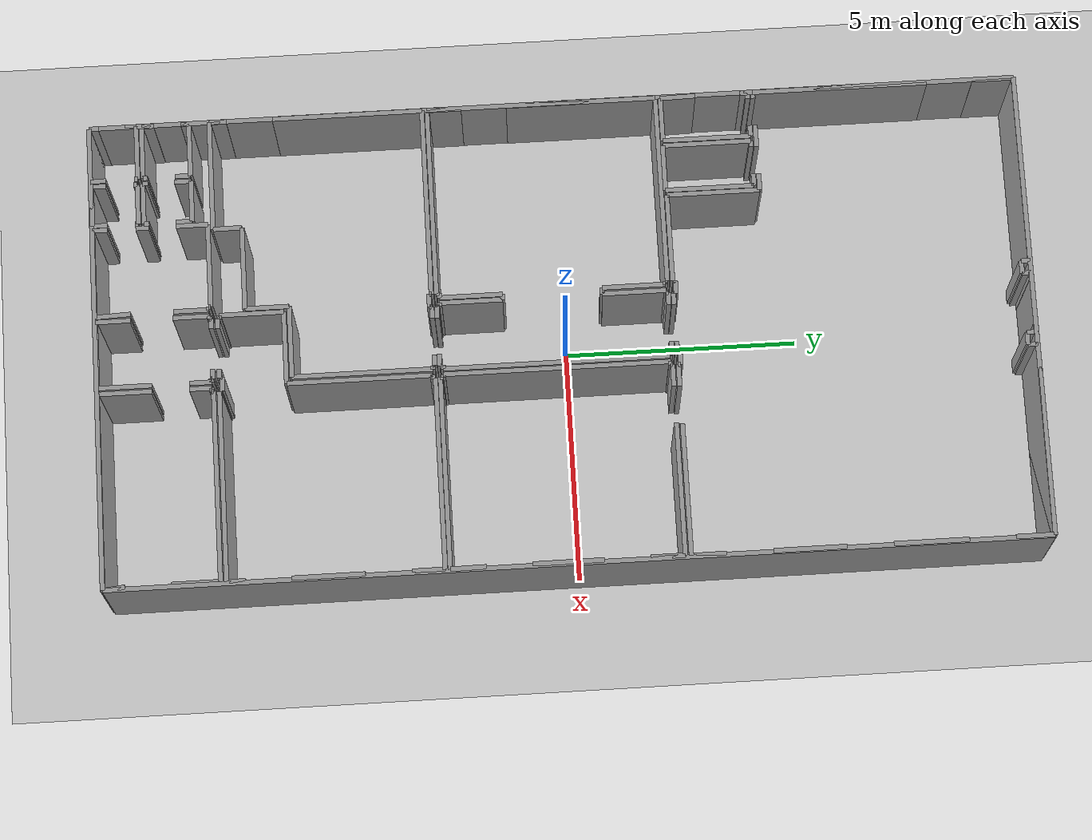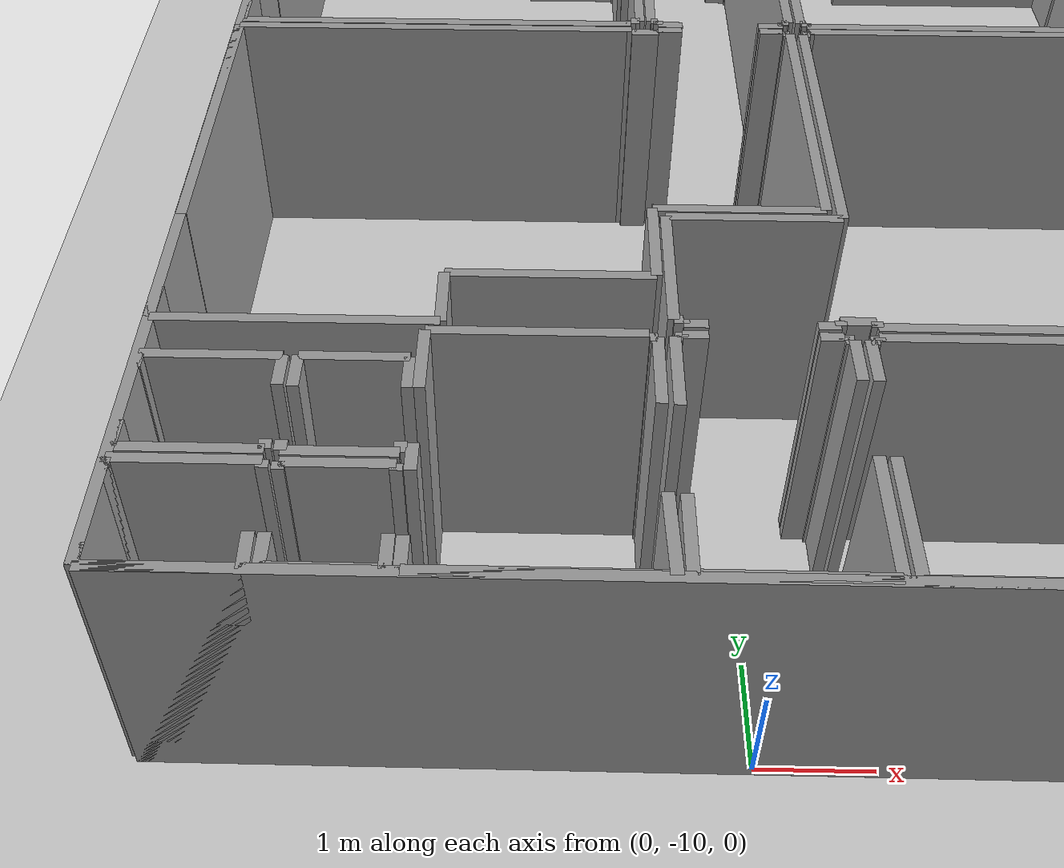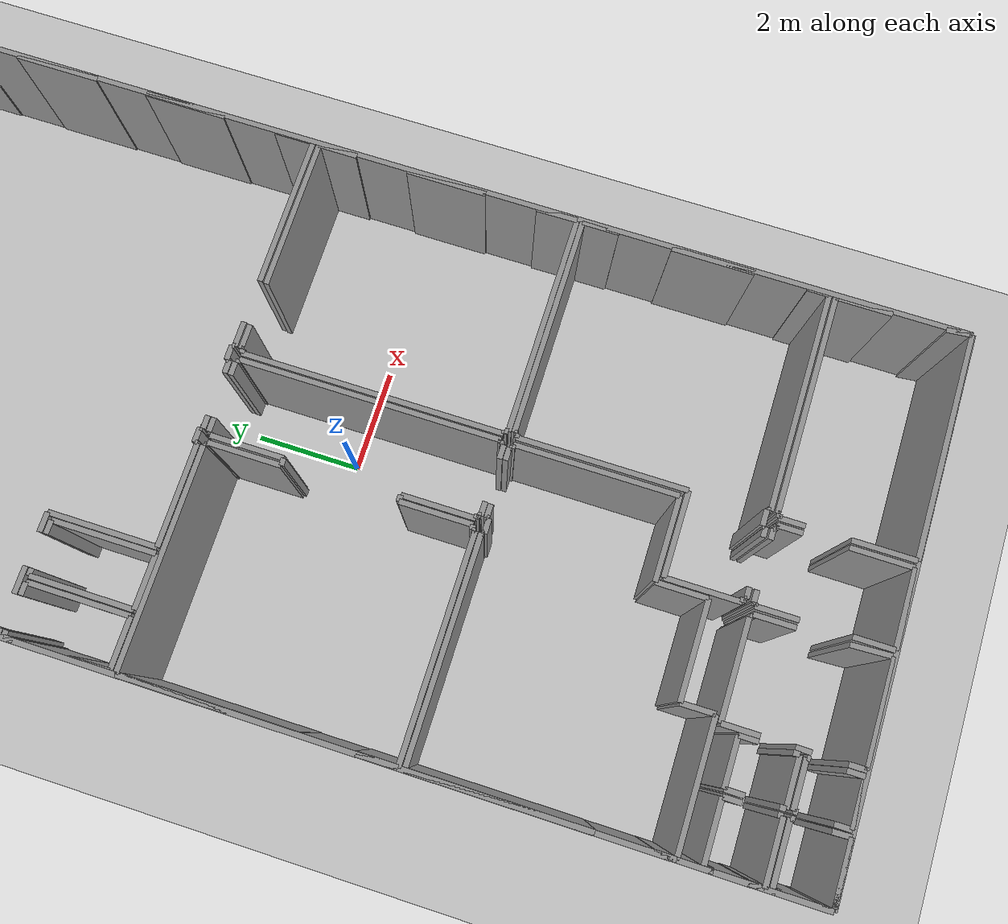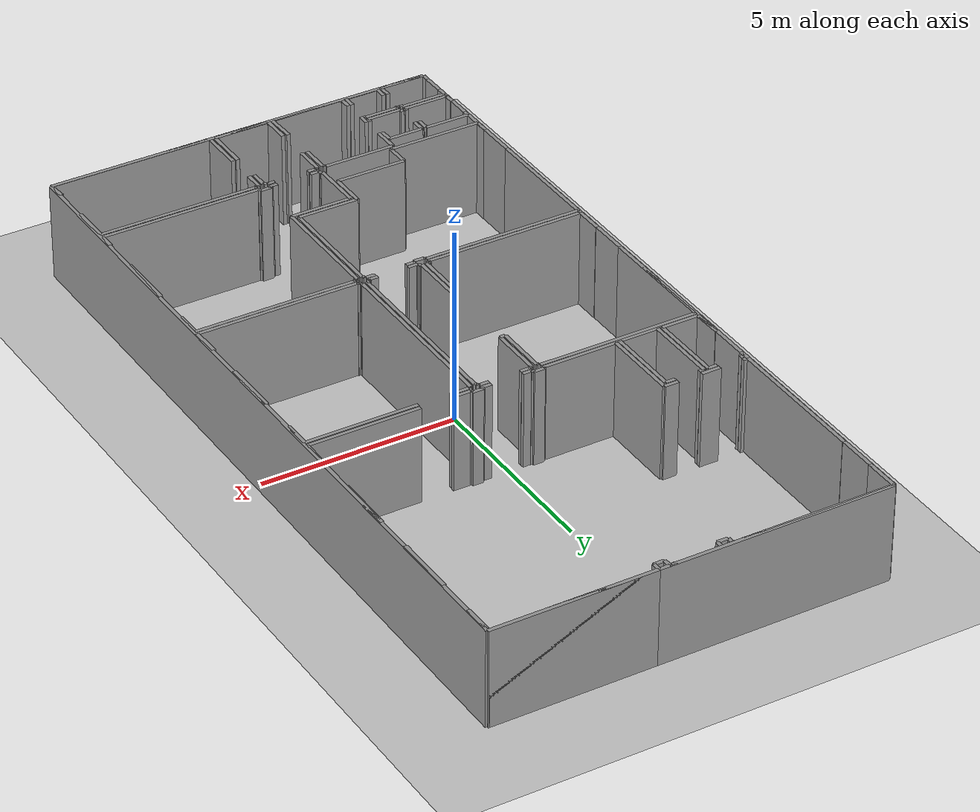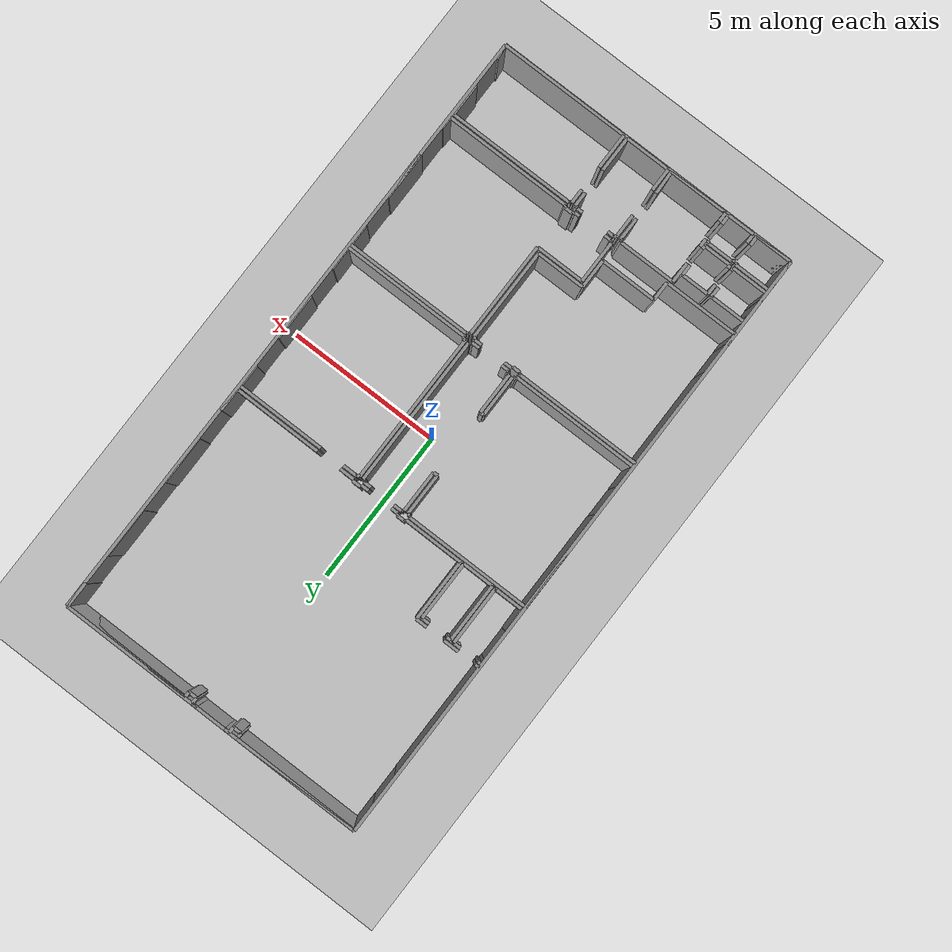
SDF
<sdf version="1.6">
  <world name="default">
    <light name="sun" type="directional">
      <cast_shadows>1</cast_shadows>
      <pose frame="">0 0 10 0 -0 0</pose>
      <diffuse>0.8 0.8 0.8 1</diffuse>
      <specular>0.1 0.1 0.1 1</specular>
      <attenuation>
        <range>1000</range>
        <constant>0.9</constant>
        <linear>0.01</linear>
        <quadratic>0.001</quadratic>
      </attenuation>
      <direction>-0.5 0.5 -1</direction>
    </light>
    <model name="ground_plane">
      <static>1</static>
      <link name="link">
        <collision name="collision">
          <geometry>
            <plane>
              <normal>0 0 1</normal>
              <size>100 100</size>
            </plane>
          </geometry>
          <surface>
            <friction>
              <ode>
                <mu>100</mu>
                <mu2>50</mu2>
              </ode>
              <torsional>
                <ode />
              </torsional>
            </friction>
            <contact>
              <ode />
            </contact>
            <bounce />
          </surface>
          <max_contacts>10</max_contacts>
        </collision>
        <visual name="visual">
          <cast_shadows>0</cast_shadows>
          <geometry>
            <plane>
              <normal>0 0 1</normal>
              <size>100 100</size>
            </plane>
          </geometry>
          <material>
            <script>
              <uri>file://media/materials/scripts/gazebo.material</uri>
              <name>Gazebo/Grey</name>
            </script>
          </material>
        </visual>
        <self_collide>0</self_collide>
        <kinematic>0</kinematic>
        <gravity>1</gravity>
      </link>
    </model>
    <gravity>0 0 -9.8</gravity>
    <magnetic_field>6e-06 2.3e-05 -4.2e-05</magnetic_field>
    <atmosphere type="adiabatic" />
    <physics default="0" name="default_physics" type="ode">
      <max_step_size>0.001</max_step_size>
      <real_time_factor>1</real_time_factor>
      <real_time_update_rate>1000</real_time_update_rate>
    </physics>
    <scene>
      <ambient>0.4 0.4 0.4 1</ambient>
      <background>0.7 0.7 0.7 1</background>
      <shadows>1</shadows>
    </scene>
    <spherical_coordinates>
      <surface_model>EARTH_WGS84</surface_model>
      <latitude_deg>0</latitude_deg>
      <longitude_deg>0</longitude_deg>
      <elevation>0</elevation>
      <heading_deg>0</heading_deg>
    </spherical_coordinates>
  <model name="50009419">
		<static>1</static>
		<link name="Wall_0">
			<collision name="Wall_0_Collision">
				<geometry>
					<box>
						<size>2.84174122724 0.1 2.5</size>
					</box>
				</geometry>
				<pose frame="">1.42087061362 0 1.25 0 0 0</pose>
			</collision>
			<visual name="Wall_0_Visual">
				<pose frame="">1.42087061362 0 1.25 0 0 0</pose>
				<geometry>
					<box>
						<size>2.84174122724 0.1 2.5</size>
					</box>
				</geometry>
				<material>
					<script>
						<uri>file://media/materials/scripts/gazebo.material</uri>
						<name>Gazebo/Grey</name>
					</script>
					<ambient>1 1 1 1</ambient>
				</material>
			</visual>
			<pose frame="">10.086997906 -7.64566279586 0 0 0 3.14159265359</pose>
		</link>
		<link name="Wall_1">
			<collision name="Wall_1_Collision">
				<geometry>
					<box>
						<size>0.470207500476 0.1 2.5</size>
					</box>
				</geometry>
				<pose frame="">0.235103750238 0 1.25 0 0 0</pose>
			</collision>
			<visual name="Wall_1_Visual">
				<pose frame="">0.235103750238 0 1.25 0 0 0</pose>
				<geometry>
					<box>
						<size>0.470207500476 0.1 2.5</size>
					</box>
				</geometry>
				<material>
					<script>
						<uri>file://media/materials/scripts/gazebo.material</uri>
						<name>Gazebo/Grey</name>
					</script>
					<ambient>1 1 1 1</ambient>
				</material>
			</visual>
			<pose frame="">6.43435497176 -7.64566279586 0 0 0 3.14159265359</pose>
		</link>
		<link name="Wall_2">
			<collision name="Wall_2_Collision">
				<geometry>
					<box>
						<size>0.0509550098357 0.1 2.5</size>
					</box>
				</geometry>
				<pose frame="">0.0254775049178 0 1.25 0 0 0</pose>
			</collision>
			<visual name="Wall_2_Visual">
				<pose frame="">0.0254775049178 0 1.25 0 0 0</pose>
				<geometry>
					<box>
						<size>0.0509550098357 0.1 2.5</size>
					</box>
				</geometry>
				<material>
					<script>
						<uri>file://media/materials/scripts/gazebo.material</uri>
						<name>Gazebo/Grey</name>
					</script>
					<ambient>1 1 1 1</ambient>
				</material>
			</visual>
			<pose frame="">5.96414747129 -7.64566279586 0 0 0 1.57079632679</pose>
		</link>
		<link name="Wall_3">
			<collision name="Wall_3_Collision">
				<geometry>
					<box>
						<size>0.273494511073 0.1 2.5</size>
					</box>
				</geometry>
				<pose frame="">0.136747255537 0 1.25 0 0 0</pose>
			</collision>
			<visual name="Wall_3_Visual">
				<pose frame="">0.136747255537 0 1.25 0 0 0</pose>
				<geometry>
					<box>
						<size>0.273494511073 0.1 2.5</size>
					</box>
				</geometry>
				<material>
					<script>
						<uri>file://media/materials/scripts/gazebo.material</uri>
						<name>Gazebo/Grey</name>
					</script>
					<ambient>1 1 1 1</ambient>
				</material>
			</visual>
			<pose frame="">5.96414747129 -7.59470778603 0 0 0 3.14159265359</pose>
		</link>
		<link name="Wall_4">
			<collision name="Wall_4_Collision">
				<geometry>
					<box>
						<size>0.0527952281236 0.1 2.5</size>
					</box>
				</geometry>
				<pose frame="">0.0263976140618 0 1.25 0 0 0</pose>
			</collision>
			<visual name="Wall_4_Visual">
				<pose frame="">0.0263976140618 0 1.25 0 0 0</pose>
				<geometry>
					<box>
						<size>0.0527952281236 0.1 2.5</size>
					</box>
				</geometry>
				<material>
					<script>
						<uri>file://media/materials/scripts/gazebo.material</uri>
						<name>Gazebo/Grey</name>
					</script>
					<ambient>1 1 1 1</ambient>
				</material>
			</visual>
			<pose frame="">5.69065296021 -7.59470778603 0 0 0 -1.57079632679</pose>
		</link>
		<link name="Wall_5">
			<collision name="Wall_5_Collision">
				<geometry>
					<box>
						<size>0.244685576496 0.1 2.5</size>
					</box>
				</geometry>
				<pose frame="">0.122342788248 0 1.25 0 0 0</pose>
			</collision>
			<visual name="Wall_5_Visual">
				<pose frame="">0.122342788248 0 1.25 0 0 0</pose>
				<geometry>
					<box>
						<size>0.244685576496 0.1 2.5</size>
					</box>
				</geometry>
				<material>
					<script>
						<uri>file://media/materials/scripts/gazebo.material</uri>
						<name>Gazebo/Grey</name>
					</script>
					<ambient>1 1 1 1</ambient>
				</material>
			</visual>
			<pose frame="">5.69065296021 -7.64750301415 0 0 0 3.14159265359</pose>
		</link>
		<link name="Wall_6">
			<collision name="Wall_6_Collision">
				<geometry>
					<box>
						<size>0.242781902405 0.1 2.5</size>
					</box>
				</geometry>
				<pose frame="">0.121390951202 0 1.25 0 0 0</pose>
			</collision>
			<visual name="Wall_6_Visual">
				<pose frame="">0.121390951202 0 1.25 0 0 0</pose>
				<geometry>
					<box>
						<size>0.242781902405 0.1 2.5</size>
					</box>
				</geometry>
				<material>
					<script>
						<uri>file://media/materials/scripts/gazebo.material</uri>
						<name>Gazebo/Grey</name>
					</script>
					<ambient>1 1 1 1</ambient>
				</material>
			</visual>
			<pose frame="">4.63360619329 -7.64750301415 0 0 0 3.14159265359</pose>
		</link>
		<link name="Wall_7">
			<collision name="Wall_7_Collision">
				<geometry>
					<box>
						<size>0.0575544133511 0.1 2.5</size>
					</box>
				</geometry>
				<pose frame="">0.0287772066756 0 1.25 0 0 0</pose>
			</collision>
			<visual name="Wall_7_Visual">
				<pose frame="">0.0287772066756 0 1.25 0 0 0</pose>
				<geometry>
					<box>
						<size>0.0575544133511 0.1 2.5</size>
					</box>
				</geometry>
				<material>
					<script>
						<uri>file://media/materials/scripts/gazebo.material</uri>
						<name>Gazebo/Grey</name>
					</script>
					<ambient>1 1 1 1</ambient>
				</material>
			</visual>
			<pose frame="">4.39082429088 -7.64750301415 0 0 0 1.57079632679</pose>
		</link>
		<link name="Wall_8">
			<collision name="Wall_8_Collision">
				<geometry>
					<box>
						<size>0.275905831588 0.1 2.5</size>
					</box>
				</geometry>
				<pose frame="">0.137952915794 0 1.25 0 0 0</pose>
			</collision>
			<visual name="Wall_8_Visual">
				<pose frame="">0.137952915794 0 1.25 0 0 0</pose>
				<geometry>
					<box>
						<size>0.275905831588 0.1 2.5</size>
					</box>
				</geometry>
				<material>
					<script>
						<uri>file://media/materials/scripts/gazebo.material</uri>
						<name>Gazebo/Grey</name>
					</script>
					<ambient>1 1 1 1</ambient>
				</material>
			</visual>
			<pose frame="">4.39082429088 -7.5899486008 0 0 0 3.14159265359</pose>
		</link>
		<link name="Wall_9">
			<collision name="Wall_9_Collision">
				<geometry>
					<box>
						<size>0.0551430928358 0.1 2.5</size>
					</box>
				</geometry>
				<pose frame="">0.0275715464179 0 1.25 0 0 0</pose>
			</collision>
			<visual name="Wall_9_Visual">
				<pose frame="">0.0275715464179 0 1.25 0 0 0</pose>
				<geometry>
					<box>
						<size>0.0551430928358 0.1 2.5</size>
					</box>
				</geometry>
				<material>
					<script>
						<uri>file://media/materials/scripts/gazebo.material</uri>
						<name>Gazebo/Grey</name>
					</script>
					<ambient>1 1 1 1</ambient>
				</material>
			</visual>
			<pose frame="">4.11491845929 -7.5899486008 0 0 0 -1.57079632679</pose>
		</link>
		<link name="Wall_10">
			<collision name="Wall_10_Collision">
				<geometry>
					<box>
						<size>1.90944856907 0.1 2.5</size>
					</box>
				</geometry>
				<pose frame="">0.954724284536 0 1.25 0 0 0</pose>
			</collision>
			<visual name="Wall_10_Visual">
				<pose frame="">0.954724284536 0 1.25 0 0 0</pose>
				<geometry>
					<box>
						<size>1.90944856907 0.1 2.5</size>
					</box>
				</geometry>
				<material>
					<script>
						<uri>file://media/materials/scripts/gazebo.material</uri>
						<name>Gazebo/Grey</name>
					</script>
					<ambient>1 1 1 1</ambient>
				</material>
			</visual>
			<pose frame="">4.11491845929 -7.64509169364 0 0 0 3.14159265359</pose>
		</link>
		<link name="Wall_11">
			<collision name="Wall_11_Collision">
				<geometry>
					<box>
						<size>1.99828669332 0.1 2.5</size>
					</box>
				</geometry>
				<pose frame="">0.999143346659 0 1.25 0 0 0</pose>
			</collision>
			<visual name="Wall_11_Visual">
				<pose frame="">0.999143346659 0 1.25 0 0 0</pose>
				<geometry>
					<box>
						<size>1.99828669332 0.1 2.5</size>
					</box>
				</geometry>
				<material>
					<script>
						<uri>file://media/materials/scripts/gazebo.material</uri>
						<name>Gazebo/Grey</name>
					</script>
					<ambient>1 1 1 1</ambient>
				</material>
			</visual>
			<pose frame="">2.20546989022 -7.64509169364 0 0 0 1.57079632679</pose>
		</link>
		<link name="Wall_12">
			<collision name="Wall_12_Collision">
				<geometry>
					<box>
						<size>0.362205723713 0.1 2.5</size>
					</box>
				</geometry>
				<pose frame="">0.181102861857 0 1.25 0 0 0</pose>
			</collision>
			<visual name="Wall_12_Visual">
				<pose frame="">0.181102861857 0 1.25 0 0 0</pose>
				<geometry>
					<box>
						<size>0.362205723713 0.1 2.5</size>
					</box>
				</geometry>
				<material>
					<script>
						<uri>file://media/materials/scripts/gazebo.material</uri>
						<name>Gazebo/Grey</name>
					</script>
					<ambient>1 1 1 1</ambient>
				</material>
			</visual>
			<pose frame="">2.20546989022 -5.64680500032 0 0 0 3.14159265359</pose>
		</link>
		<link name="Wall_13">
			<collision name="Wall_13_Collision">
				<geometry>
					<box>
						<size>0.495335998477 0.1 2.5</size>
					</box>
				</geometry>
				<pose frame="">0.247667999239 0 1.25 0 0 0</pose>
			</collision>
			<visual name="Wall_13_Visual">
				<pose frame="">0.247667999239 0 1.25 0 0 0</pose>
				<geometry>
					<box>
						<size>0.495335998477 0.1 2.5</size>
					</box>
				</geometry>
				<material>
					<script>
						<uri>file://media/materials/scripts/gazebo.material</uri>
						<name>Gazebo/Grey</name>
					</script>
					<ambient>1 1 1 1</ambient>
				</material>
			</visual>
			<pose frame="">1.2344057364 -5.64680500032 0 0 0 3.14159265359</pose>
		</link>
		<link name="Wall_14">
			<collision name="Wall_14_Collision">
				<geometry>
					<box>
						<size>0.132495716733 0.1 2.5</size>
					</box>
				</geometry>
				<pose frame="">0.0662478583666 0 1.25 0 0 0</pose>
			</collision>
			<visual name="Wall_14_Visual">
				<pose frame="">0.0662478583666 0 1.25 0 0 0</pose>
				<geometry>
					<box>
						<size>0.132495716733 0.1 2.5</size>
					</box>
				</geometry>
				<material>
					<script>
						<uri>file://media/materials/scripts/gazebo.material</uri>
						<name>Gazebo/Grey</name>
					</script>
					<ambient>1 1 1 1</ambient>
				</material>
			</visual>
			<pose frame="">0.139666222476 -5.64680500032 0 0 0 3.14159265359</pose>
		</link>
		<link name="Wall_15">
			<collision name="Wall_15_Collision">
				<geometry>
					<box>
						<size>3.76648264484 0.1 2.5</size>
					</box>
				</geometry>
				<pose frame="">1.88324132242 0 1.25 0 0 0</pose>
			</collision>
			<visual name="Wall_15_Visual">
				<pose frame="">1.88324132242 0 1.25 0 0 0</pose>
				<geometry>
					<box>
						<size>3.76648264484 0.1 2.5</size>
					</box>
				</geometry>
				<material>
					<script>
						<uri>file://media/materials/scripts/gazebo.material</uri>
						<name>Gazebo/Grey</name>
					</script>
					<ambient>1 1 1 1</ambient>
				</material>
			</visual>
			<pose frame="">0.00717050574275 -5.64680500032 0 0 0 1.57079632679</pose>
		</link>
		<link name="Wall_16">
			<collision name="Wall_16_Collision">
				<geometry>
					<box>
						<size>0.89561520401 0.1 2.5</size>
					</box>
				</geometry>
				<pose frame="">0.447807602005 0 1.25 0 0 0</pose>
			</collision>
			<visual name="Wall_16_Visual">
				<pose frame="">0.447807602005 0 1.25 0 0 0</pose>
				<geometry>
					<box>
						<size>0.89561520401 0.1 2.5</size>
					</box>
				</geometry>
				<material>
					<script>
						<uri>file://media/materials/scripts/gazebo.material</uri>
						<name>Gazebo/Grey</name>
					</script>
					<ambient>1 1 1 1</ambient>
				</material>
			</visual>
			<pose frame="">0.00717050574275 -0.898470715147 0 0 0 1.57079632679</pose>
		</link>
		<link name="Wall_17">
			<collision name="Wall_17_Collision">
				<geometry>
					<box>
						<size>4.10774795355 0.1 2.5</size>
					</box>
				</geometry>
				<pose frame="">2.05387397678 0 1.25 0 0 0</pose>
			</collision>
			<visual name="Wall_17_Visual">
				<pose frame="">2.05387397678 0 1.25 0 0 0</pose>
				<geometry>
					<box>
						<size>4.10774795355 0.1 2.5</size>
					</box>
				</geometry>
				<material>
					<script>
						<uri>file://media/materials/scripts/gazebo.material</uri>
						<name>Gazebo/Grey</name>
					</script>
					<ambient>1 1 1 1</ambient>
				</material>
			</visual>
			<pose frame="">0.00717050574275 -0.00285551113649 0 0 0 0.0</pose>
		</link>
		<link name="Wall_18">
			<collision name="Wall_18_Collision">
				<geometry>
					<box>
						<size>0.188273367599 0.1 2.5</size>
					</box>
				</geometry>
				<pose frame="">0.0941366837997 0 1.25 0 0 0</pose>
			</collision>
			<visual name="Wall_18_Visual">
				<pose frame="">0.0941366837997 0 1.25 0 0 0</pose>
				<geometry>
					<box>
						<size>0.188273367599 0.1 2.5</size>
					</box>
				</geometry>
				<material>
					<script>
						<uri>file://media/materials/scripts/gazebo.material</uri>
						<name>Gazebo/Grey</name>
					</script>
					<ambient>1 1 1 1</ambient>
				</material>
			</visual>
			<pose frame="">4.11491845929 -0.00285551113649 0 0 0 -1.57079632679</pose>
		</link>
		<link name="Wall_19">
			<collision name="Wall_19_Collision">
				<geometry>
					<box>
						<size>0.270638999937 0.1 2.5</size>
					</box>
				</geometry>
				<pose frame="">0.135319499968 0 1.25 0 0 0</pose>
			</collision>
			<visual name="Wall_19_Visual">
				<pose frame="">0.135319499968 0 1.25 0 0 0</pose>
				<geometry>
					<box>
						<size>0.270638999937 0.1 2.5</size>
					</box>
				</geometry>
				<material>
					<script>
						<uri>file://media/materials/scripts/gazebo.material</uri>
						<name>Gazebo/Grey</name>
					</script>
					<ambient>1 1 1 1</ambient>
				</material>
			</visual>
			<pose frame="">4.11491845929 -0.191128878736 0 0 0 0.0</pose>
		</link>
		<link name="Wall_20">
			<collision name="Wall_20_Collision">
				<geometry>
					<box>
						<size>0.182308522114 0.1 2.5</size>
					</box>
				</geometry>
				<pose frame="">0.0911542610572 0 1.25 0 0 0</pose>
			</collision>
			<visual name="Wall_20_Visual">
				<pose frame="">0.0911542610572 0 1.25 0 0 0</pose>
				<geometry>
					<box>
						<size>0.182308522114 0.1 2.5</size>
					</box>
				</geometry>
				<material>
					<script>
						<uri>file://media/materials/scripts/gazebo.material</uri>
						<name>Gazebo/Grey</name>
					</script>
					<ambient>1 1 1 1</ambient>
				</material>
			</visual>
			<pose frame="">4.38555745923 -0.191128878736 0 0 0 1.57079632679</pose>
		</link>
		<link name="Wall_21">
			<collision name="Wall_21_Collision">
				<geometry>
					<box>
						<size>0.164604353068 0.1 2.5</size>
					</box>
				</geometry>
				<pose frame="">0.082302176534 0 1.25 0 0 0</pose>
			</collision>
			<visual name="Wall_21_Visual">
				<pose frame="">0.082302176534 0 1.25 0 0 0</pose>
				<geometry>
					<box>
						<size>0.164604353068 0.1 2.5</size>
					</box>
				</geometry>
				<material>
					<script>
						<uri>file://media/materials/scripts/gazebo.material</uri>
						<name>Gazebo/Grey</name>
					</script>
					<ambient>1 1 1 1</ambient>
				</material>
			</visual>
			<pose frame="">4.38555745923 -0.00882035662161 0 0 0 0.0</pose>
		</link>
		<link name="Wall_22">
			<collision name="Wall_22_Collision">
				<geometry>
					<box>
						<size>0.17050574275 0.1 2.5</size>
					</box>
				</geometry>
				<pose frame="">0.0852528713751 0 1.25 0 0 0</pose>
			</collision>
			<visual name="Wall_22_Visual">
				<pose frame="">0.0852528713751 0 1.25 0 0 0</pose>
				<geometry>
					<box>
						<size>0.17050574275 0.1 2.5</size>
					</box>
				</geometry>
				<material>
					<script>
						<uri>file://media/materials/scripts/gazebo.material</uri>
						<name>Gazebo/Grey</name>
					</script>
					<ambient>1 1 1 1</ambient>
				</material>
			</visual>
			<pose frame="">5.5188781014 -0.00882035662161 0 0 0 0.0</pose>
		</link>
		<link name="Wall_23">
			<collision name="Wall_23_Collision">
				<geometry>
					<box>
						<size>0.194365124691 0.1 2.5</size>
					</box>
				</geometry>
				<pose frame="">0.0971825623453 0 1.25 0 0 0</pose>
			</collision>
			<visual name="Wall_23_Visual">
				<pose frame="">0.0971825623453 0 1.25 0 0 0</pose>
				<geometry>
					<box>
						<size>0.194365124691 0.1 2.5</size>
					</box>
				</geometry>
				<material>
					<script>
						<uri>file://media/materials/scripts/gazebo.material</uri>
						<name>Gazebo/Grey</name>
					</script>
					<ambient>1 1 1 1</ambient>
				</material>
			</visual>
			<pose frame="">5.68938384415 -0.00882035662161 0 0 0 -1.57079632679</pose>
		</link>
		<link name="Wall_24">
			<collision name="Wall_24_Collision">
				<geometry>
					<box>
						<size>0.264864521861 0.1 2.5</size>
					</box>
				</geometry>
				<pose frame="">0.13243226093 0 1.25 0 0 0</pose>
			</collision>
			<visual name="Wall_24_Visual">
				<pose frame="">0.13243226093 0 1.25 0 0 0</pose>
				<geometry>
					<box>
						<size>0.264864521861 0.1 2.5</size>
					</box>
				</geometry>
				<material>
					<script>
						<uri>file://media/materials/scripts/gazebo.material</uri>
						<name>Gazebo/Grey</name>
					</script>
					<ambient>1 1 1 1</ambient>
				</material>
			</visual>
			<pose frame="">5.68938384415 -0.203185481312 0 0 0 0.0</pose>
		</link>
		<link name="Wall_25">
			<collision name="Wall_25_Collision">
				<geometry>
					<box>
						<size>0.203185481312 0.1 2.5</size>
					</box>
				</geometry>
				<pose frame="">0.101592740656 0 1.25 0 0 0</pose>
			</collision>
			<visual name="Wall_25_Visual">
				<pose frame="">0.101592740656 0 1.25 0 0 0</pose>
				<geometry>
					<box>
						<size>0.203185481312 0.1 2.5</size>
					</box>
				</geometry>
				<material>
					<script>
						<uri>file://media/materials/scripts/gazebo.material</uri>
						<name>Gazebo/Grey</name>
					</script>
					<ambient>1 1 1 1</ambient>
				</material>
			</visual>
			<pose frame="">5.95424836601 -0.203185481312 0 0 0 1.57079632679</pose>
		</link>
		<link name="Wall_26">
			<collision name="Wall_26_Collision">
				<geometry>
					<box>
						<size>4.13103623326 0.1 2.5</size>
					</box>
				</geometry>
				<pose frame="">2.06551811663 0 1.25 0 0 0</pose>
			</collision>
			<visual name="Wall_26_Visual">
				<pose frame="">2.06551811663 0 1.25 0 0 0</pose>
				<geometry>
					<box>
						<size>4.13103623326 0.1 2.5</size>
					</box>
				</geometry>
				<material>
					<script>
						<uri>file://media/materials/scripts/gazebo.material</uri>
						<name>Gazebo/Grey</name>
					</script>
					<ambient>1 1 1 1</ambient>
				</material>
			</visual>
			<pose frame="">5.95424836601 -0.0 0 0 0 0.0</pose>
		</link>
		<link name="Wall_27">
			<collision name="Wall_27_Collision">
				<geometry>
					<box>
						<size>0.814899422552 0.1 2.5</size>
					</box>
				</geometry>
				<pose frame="">0.407449711276 0 1.25 0 0 0</pose>
			</collision>
			<visual name="Wall_27_Visual">
				<pose frame="">0.407449711276 0 1.25 0 0 0</pose>
				<geometry>
					<box>
						<size>0.814899422552 0.1 2.5</size>
					</box>
				</geometry>
				<material>
					<script>
						<uri>file://media/materials/scripts/gazebo.material</uri>
						<name>Gazebo/Grey</name>
					</script>
					<ambient>1 1 1 1</ambient>
				</material>
			</visual>
			<pose frame="">10.0852845993 -0.0 0 0 0 -1.57079632679</pose>
		</link>
		<link name="Wall_28">
			<collision name="Wall_28_Collision">
				<geometry>
					<box>
						<size>1.59299447935 0.1 2.5</size>
					</box>
				</geometry>
				<pose frame="">0.796497239673 0 1.25 0 0 0</pose>
			</collision>
			<visual name="Wall_28_Visual">
				<pose frame="">0.796497239673 0 1.25 0 0 0</pose>
				<geometry>
					<box>
						<size>1.59299447935 0.1 2.5</size>
					</box>
				</geometry>
				<material>
					<script>
						<uri>file://media/materials/scripts/gazebo.material</uri>
						<name>Gazebo/Grey</name>
					</script>
					<ambient>1 1 1 1</ambient>
				</material>
			</visual>
			<pose frame="">10.0852845993 -1.79852782537 0 0 0 -1.57079632679</pose>
		</link>
		<link name="Wall_29">
			<collision name="Wall_29_Collision">
				<geometry>
					<box>
						<size>1.54502189225 0.1 2.5</size>
					</box>
				</geometry>
				<pose frame="">0.772510946126 0 1.25 0 0 0</pose>
			</collision>
			<visual name="Wall_29_Visual">
				<pose frame="">0.772510946126 0 1.25 0 0 0</pose>
				<geometry>
					<box>
						<size>1.54502189225 0.1 2.5</size>
					</box>
				</geometry>
				<material>
					<script>
						<uri>file://media/materials/scripts/gazebo.material</uri>
						<name>Gazebo/Grey</name>
					</script>
					<ambient>1 1 1 1</ambient>
				</material>
			</visual>
			<pose frame="">10.0852845993 -4.3703280665 0 0 0 -1.57079632679</pose>
		</link>
		<link name="Wall_30">
			<collision name="Wall_30_Collision">
				<geometry>
					<box>
						<size>0.741863771673 0.1 2.5</size>
					</box>
				</geometry>
				<pose frame="">0.370931885836 0 1.25 0 0 0</pose>
			</collision>
			<visual name="Wall_30_Visual">
				<pose frame="">0.370931885836 0 1.25 0 0 0</pose>
				<geometry>
					<box>
						<size>0.741863771673 0.1 2.5</size>
					</box>
				</geometry>
				<material>
					<script>
						<uri>file://media/materials/scripts/gazebo.material</uri>
						<name>Gazebo/Grey</name>
					</script>
					<ambient>1 1 1 1</ambient>
				</material>
			</visual>
			<pose frame="">10.0852845993 -6.9038010026 0 0 0 -1.56848686208</pose>
		</link>
		<link name="Wall_31">
			<collision name="Wall_31_Collision">
				<geometry>
					<box>
						<size>1.903674091 0.1 2.5</size>
					</box>
				</geometry>
				<pose frame="">0.951837045498 0 1.25 0 0 0</pose>
			</collision>
			<visual name="Wall_31_Visual">
				<pose frame="">0.951837045498 0 1.25 0 0 0</pose>
				<geometry>
					<box>
						<size>1.903674091 0.1 2.5</size>
					</box>
				</geometry>
				<material>
					<script>
						<uri>file://media/materials/scripts/gazebo.material</uri>
						<name>Gazebo/Grey</name>
					</script>
					<ambient>1 1 1 1</ambient>
				</material>
			</visual>
			<pose frame="">2.09759502507 -7.66469953677 0 0 0 1.57079632679</pose>
		</link>
		<link name="Wall_32">
			<collision name="Wall_32_Collision">
				<geometry>
					<box>
						<size>0.255092328193 0.1 2.5</size>
					</box>
				</geometry>
				<pose frame="">0.127546164097 0 1.25 0 0 0</pose>
			</collision>
			<visual name="Wall_32_Visual">
				<pose frame="">0.127546164097 0 1.25 0 0 0</pose>
				<geometry>
					<box>
						<size>0.255092328193 0.1 2.5</size>
					</box>
				</geometry>
				<material>
					<script>
						<uri>file://media/materials/scripts/gazebo.material</uri>
						<name>Gazebo/Grey</name>
					</script>
					<ambient>1 1 1 1</ambient>
				</material>
			</visual>
			<pose frame="">2.09759502507 -5.76102544578 0 0 0 3.14159265359</pose>
		</link>
		<link name="Wall_33">
			<collision name="Wall_33_Collision">
				<geometry>
					<box>
						<size>0.13243226093 0.1 2.5</size>
					</box>
				</geometry>
				<pose frame="">0.0662161304651 0 1.25 0 0 0</pose>
			</collision>
			<visual name="Wall_33_Visual">
				<pose frame="">0.0662161304651 0 1.25 0 0 0</pose>
				<geometry>
					<box>
						<size>0.13243226093 0.1 2.5</size>
					</box>
				</geometry>
				<material>
					<script>
						<uri>file://media/materials/scripts/gazebo.material</uri>
						<name>Gazebo/Grey</name>
					</script>
					<ambient>1 1 1 1</ambient>
				</material>
			</visual>
			<pose frame="">1.22907544895 -5.76102544578 0 0 0 3.14159265359</pose>
		</link>
		<link name="Wall_34">
			<collision name="Wall_34_Collision">
				<geometry>
					<box>
						<size>1.90062821245 0.1 2.5</size>
					</box>
				</geometry>
				<pose frame="">0.950314106225 0 1.25 0 0 0</pose>
			</collision>
			<visual name="Wall_34_Visual">
				<pose frame="">0.950314106225 0 1.25 0 0 0</pose>
				<geometry>
					<box>
						<size>1.90062821245 0.1 2.5</size>
					</box>
				</geometry>
				<material>
					<script>
						<uri>file://media/materials/scripts/gazebo.material</uri>
						<name>Gazebo/Grey</name>
					</script>
					<ambient>1 1 1 1</ambient>
				</material>
			</visual>
			<pose frame="">1.09664318802 -5.76102544578 0 0 0 -1.57079632679</pose>
		</link>
		<link name="Wall_35">
			<collision name="Wall_35_Collision">
				<geometry>
					<box>
						<size>1.00095647131 0.1 2.5</size>
					</box>
				</geometry>
				<pose frame="">0.500478235656 0 1.25 0 0 0</pose>
			</collision>
			<visual name="Wall_35_Visual">
				<pose frame="">0.500478235656 0 1.25 0 0 0</pose>
				<geometry>
					<box>
						<size>1.00095647131 0.1 2.5</size>
					</box>
				</geometry>
				<material>
					<script>
						<uri>file://media/materials/scripts/gazebo.material</uri>
						<name>Gazebo/Grey</name>
					</script>
					<ambient>1 1 1 1</ambient>
				</material>
			</visual>
			<pose frame="">1.09664318802 -7.66165365823 0 0 0 -0.00304297273012</pose>
		</link>
		<link name="Wall_36">
			<collision name="Wall_36_Collision">
				<geometry>
					<box>
						<size>0.95481946824 0.1 2.5</size>
					</box>
				</geometry>
				<pose frame="">0.47740973412 0 1.25 0 0 0</pose>
			</collision>
			<visual name="Wall_36_Visual">
				<pose frame="">0.47740973412 0 1.25 0 0 0</pose>
				<geometry>
					<box>
						<size>0.95481946824 0.1 2.5</size>
					</box>
				</geometry>
				<material>
					<script>
						<uri>file://media/materials/scripts/gazebo.material</uri>
						<name>Gazebo/Grey</name>
					</script>
					<ambient>1 1 1 1</ambient>
				</material>
			</visual>
			<pose frame="">0.0288089345771 -7.64750301415 0 0 0 0.0</pose>
		</link>
		<link name="Wall_37">
			<collision name="Wall_37_Collision">
				<geometry>
					<box>
						<size>1.89047528396 0.1 2.5</size>
					</box>
				</geometry>
				<pose frame="">0.945237641982 0 1.25 0 0 0</pose>
			</collision>
			<visual name="Wall_37_Visual">
				<pose frame="">0.945237641982 0 1.25 0 0 0</pose>
				<geometry>
					<box>
						<size>1.89047528396 0.1 2.5</size>
					</box>
				</geometry>
				<material>
					<script>
						<uri>file://media/materials/scripts/gazebo.material</uri>
						<name>Gazebo/Grey</name>
					</script>
					<ambient>1 1 1 1</ambient>
				</material>
			</visual>
			<pose frame="">0.983628402817 -7.64750301415 0 0 0 1.57079632679</pose>
		</link>
		<link name="Wall_38">
			<collision name="Wall_38_Collision">
				<geometry>
					<box>
						<size>0.235103750238 0.1 2.5</size>
					</box>
				</geometry>
				<pose frame="">0.117551875119 0 1.25 0 0 0</pose>
			</collision>
			<visual name="Wall_38_Visual">
				<pose frame="">0.117551875119 0 1.25 0 0 0</pose>
				<geometry>
					<box>
						<size>0.235103750238 0.1 2.5</size>
					</box>
				</geometry>
				<material>
					<script>
						<uri>file://media/materials/scripts/gazebo.material</uri>
						<name>Gazebo/Grey</name>
					</script>
					<ambient>1 1 1 1</ambient>
				</material>
			</visual>
			<pose frame="">0.983628402817 -5.75702773019 0 0 0 3.14159265359</pose>
		</link>
		<link name="Wall_39">
			<collision name="Wall_39_Collision">
				<geometry>
					<box>
						<size>0.126975061869 0.1 2.5</size>
					</box>
				</geometry>
				<pose frame="">0.0634875309347 0 1.25 0 0 0</pose>
			</collision>
			<visual name="Wall_39_Visual">
				<pose frame="">0.0634875309347 0 1.25 0 0 0</pose>
				<geometry>
					<box>
						<size>0.126975061869 0.1 2.5</size>
					</box>
				</geometry>
				<material>
					<script>
						<uri>file://media/materials/scripts/gazebo.material</uri>
						<name>Gazebo/Grey</name>
					</script>
					<ambient>1 1 1 1</ambient>
				</material>
			</visual>
			<pose frame="">0.138397106415 -5.75702773019 0 0 0 3.14159265359</pose>
		</link>
		<link name="Wall_40">
			<collision name="Wall_40_Collision">
				<geometry>
					<box>
						<size>0.164033250841 0.1 2.5</size>
					</box>
				</geometry>
				<pose frame="">0.0820166254204 0 1.25 0 0 0</pose>
			</collision>
			<visual name="Wall_40_Visual">
				<pose frame="">0.0820166254204 0 1.25 0 0 0</pose>
				<geometry>
					<box>
						<size>0.164033250841 0.1 2.5</size>
					</box>
				</geometry>
				<material>
					<script>
						<uri>file://media/materials/scripts/gazebo.material</uri>
						<name>Gazebo/Grey</name>
					</script>
					<ambient>1 1 1 1</ambient>
				</material>
			</visual>
			<pose frame="">0.011422044546 -5.75702773019 0 0 0 -1.57079632679</pose>
		</link>
		<link name="Wall_41">
			<collision name="Wall_41_Collision">
				<geometry>
					<box>
						<size>0.75430917451 0.1 2.5</size>
					</box>
				</geometry>
				<pose frame="">0.377154587255 0 1.25 0 0 0</pose>
			</collision>
			<visual name="Wall_41_Visual">
				<pose frame="">0.377154587255 0 1.25 0 0 0</pose>
				<geometry>
					<box>
						<size>0.75430917451 0.1 2.5</size>
					</box>
				</geometry>
				<material>
					<script>
						<uri>file://media/materials/scripts/gazebo.material</uri>
						<name>Gazebo/Grey</name>
					</script>
					<ambient>1 1 1 1</ambient>
				</material>
			</visual>
			<pose frame="">0.011422044546 -6.8933942509 0 0 0 -1.54774420094</pose>
		</link>
		<link name="Wall_42">
			<collision name="Wall_42_Collision">
				<geometry>
					<box>
						<size>0.260232248239 0.1 2.5</size>
					</box>
				</geometry>
				<pose frame="">0.13011612412 0 1.25 0 0 0</pose>
			</collision>
			<visual name="Wall_42_Visual">
				<pose frame="">0.13011612412 0 1.25 0 0 0</pose>
				<geometry>
					<box>
						<size>0.260232248239 0.1 2.5</size>
					</box>
				</geometry>
				<material>
					<script>
						<uri>file://media/materials/scripts/gazebo.material</uri>
						<name>Gazebo/Grey</name>
					</script>
					<ambient>1 1 1 1</ambient>
				</material>
			</visual>
			<pose frame="">5.69395266197 -12.6954756012 0 0 0 3.14159265359</pose>
		</link>
		<link name="Wall_43">
			<collision name="Wall_43_Collision">
				<geometry>
					<box>
						<size>0.255409607209 0.1 2.5</size>
					</box>
				</geometry>
				<pose frame="">0.127704803604 0 1.25 0 0 0</pose>
			</collision>
			<visual name="Wall_43_Visual">
				<pose frame="">0.127704803604 0 1.25 0 0 0</pose>
				<geometry>
					<box>
						<size>0.255409607209 0.1 2.5</size>
					</box>
				</geometry>
				<material>
					<script>
						<uri>file://media/materials/scripts/gazebo.material</uri>
						<name>Gazebo/Grey</name>
					</script>
					<ambient>1 1 1 1</ambient>
				</material>
			</visual>
			<pose frame="">4.64312456374 -12.6954756012 0 0 0 3.14159265359</pose>
		</link>
		<link name="Wall_44">
			<collision name="Wall_44_Collision">
				<geometry>
					<box>
						<size>0.0626943333968 0.1 2.5</size>
					</box>
				</geometry>
				<pose frame="">0.0313471666984 0 1.25 0 0 0</pose>
			</collision>
			<visual name="Wall_44_Visual">
				<pose frame="">0.0313471666984 0 1.25 0 0 0</pose>
				<geometry>
					<box>
						<size>0.0626943333968 0.1 2.5</size>
					</box>
				</geometry>
				<material>
					<script>
						<uri>file://media/materials/scripts/gazebo.material</uri>
						<name>Gazebo/Grey</name>
					</script>
					<ambient>1 1 1 1</ambient>
				</material>
			</visual>
			<pose frame="">4.38771495653 -12.6954756012 0 0 0 1.57079632679</pose>
		</link>
		<link name="Wall_45">
			<collision name="Wall_45_Collision">
				<geometry>
					<box>
						<size>0.0741163779428 0.1 2.5</size>
					</box>
				</geometry>
				<pose frame="">0.0370581889714 0 1.25 0 0 0</pose>
			</collision>
			<visual name="Wall_45_Visual">
				<pose frame="">0.0370581889714 0 1.25 0 0 0</pose>
				<geometry>
					<box>
						<size>0.0741163779428 0.1 2.5</size>
					</box>
				</geometry>
				<material>
					<script>
						<uri>file://media/materials/scripts/gazebo.material</uri>
						<name>Gazebo/Grey</name>
					</script>
					<ambient>1 1 1 1</ambient>
				</material>
			</visual>
			<pose frame="">4.38771495653 -12.6327812678 0 0 0 3.14159265359</pose>
		</link>
		<link name="Wall_46">
			<collision name="Wall_46_Collision">
				<geometry>
					<box>
						<size>1.34824544705 0.1 2.5</size>
					</box>
				</geometry>
				<pose frame="">0.674122723523 0 1.25 0 0 0</pose>
			</collision>
			<visual name="Wall_46_Visual">
				<pose frame="">0.674122723523 0 1.25 0 0 0</pose>
				<geometry>
					<box>
						<size>1.34824544705 0.1 2.5</size>
					</box>
				</geometry>
				<material>
					<script>
						<uri>file://media/materials/scripts/gazebo.material</uri>
						<name>Gazebo/Grey</name>
					</script>
					<ambient>1 1 1 1</ambient>
				</material>
			</visual>
			<pose frame="">4.31359857859 -12.6327812678 0 0 0 1.57079632679</pose>
		</link>
		<link name="Wall_47">
			<collision name="Wall_47_Collision">
				<geometry>
					<box>
						<size>0.115172282505 0.1 2.5</size>
					</box>
				</geometry>
				<pose frame="">0.0575861412526 0 1.25 0 0 0</pose>
			</collision>
			<visual name="Wall_47_Visual">
				<pose frame="">0.0575861412526 0 1.25 0 0 0</pose>
				<geometry>
					<box>
						<size>0.115172282505 0.1 2.5</size>
					</box>
				</geometry>
				<material>
					<script>
						<uri>file://media/materials/scripts/gazebo.material</uri>
						<name>Gazebo/Grey</name>
					</script>
					<ambient>1 1 1 1</ambient>
				</material>
			</visual>
			<pose frame="">4.31359857859 -11.2845358208 0 0 0 3.14159265359</pose>
		</link>
		<link name="Wall_48">
			<collision name="Wall_48_Collision">
				<geometry>
					<box>
						<size>1.33936163462 0.1 2.5</size>
					</box>
				</geometry>
				<pose frame="">0.669680817311 0 1.25 0 0 0</pose>
			</collision>
			<visual name="Wall_48_Visual">
				<pose frame="">0.669680817311 0 1.25 0 0 0</pose>
				<geometry>
					<box>
						<size>1.33936163462 0.1 2.5</size>
					</box>
				</geometry>
				<material>
					<script>
						<uri>file://media/materials/scripts/gazebo.material</uri>
						<name>Gazebo/Grey</name>
					</script>
					<ambient>1 1 1 1</ambient>
				</material>
			</visual>
			<pose frame="">4.19842629608 -11.2845358208 0 0 0 -1.57079632679</pose>
		</link>
		<link name="Wall_49">
			<collision name="Wall_49_Collision">
				<geometry>
					<box>
						<size>0.0930896630497 0.1 2.5</size>
					</box>
				</geometry>
				<pose frame="">0.0465448315248 0 1.25 0 0 0</pose>
			</collision>
			<visual name="Wall_49_Visual">
				<pose frame="">0.0465448315248 0 1.25 0 0 0</pose>
				<geometry>
					<box>
						<size>0.0930896630497 0.1 2.5</size>
					</box>
				</geometry>
				<material>
					<script>
						<uri>file://media/materials/scripts/gazebo.material</uri>
						<name>Gazebo/Grey</name>
					</script>
					<ambient>1 1 1 1</ambient>
				</material>
			</visual>
			<pose frame="">4.19842629608 -12.6238974554 0 0 0 3.14159265359</pose>
		</link>
		<link name="Wall_50">
			<collision name="Wall_50_Collision">
				<geometry>
					<box>
						<size>0.063075068215 0.1 2.5</size>
					</box>
				</geometry>
				<pose frame="">0.0315375341075 0 1.25 0 0 0</pose>
			</collision>
			<visual name="Wall_50_Visual">
				<pose frame="">0.0315375341075 0 1.25 0 0 0</pose>
				<geometry>
					<box>
						<size>0.063075068215 0.1 2.5</size>
					</box>
				</geometry>
				<material>
					<script>
						<uri>file://media/materials/scripts/gazebo.material</uri>
						<name>Gazebo/Grey</name>
					</script>
					<ambient>1 1 1 1</ambient>
				</material>
			</visual>
			<pose frame="">4.10533663304 -12.6238974554 0 0 0 -1.57079632679</pose>
		</link>
		<link name="Wall_51">
			<collision name="Wall_51_Collision">
				<geometry>
					<box>
						<size>4.09759502507 0.1 2.5</size>
					</box>
				</geometry>
				<pose frame="">2.04879751253 0 1.25 0 0 0</pose>
			</collision>
			<visual name="Wall_51_Visual">
				<pose frame="">2.04879751253 0 1.25 0 0 0</pose>
				<geometry>
					<box>
						<size>4.09759502507 0.1 2.5</size>
					</box>
				</geometry>
				<material>
					<script>
						<uri>file://media/materials/scripts/gazebo.material</uri>
						<name>Gazebo/Grey</name>
					</script>
					<ambient>1 1 1 1</ambient>
				</material>
			</visual>
			<pose frame="">4.10533663304 -12.6869725236 0 0 0 3.14159265359</pose>
		</link>
		<link name="Wall_52">
			<collision name="Wall_52_Collision">
				<geometry>
					<box>
						<size>0.736023859382 0.1 2.5</size>
					</box>
				</geometry>
				<pose frame="">0.368011929691 0 1.25 0 0 0</pose>
			</collision>
			<visual name="Wall_52_Visual">
				<pose frame="">0.368011929691 0 1.25 0 0 0</pose>
				<geometry>
					<box>
						<size>0.736023859382 0.1 2.5</size>
					</box>
				</geometry>
				<material>
					<script>
						<uri>file://media/materials/scripts/gazebo.material</uri>
						<name>Gazebo/Grey</name>
					</script>
					<ambient>1 1 1 1</ambient>
				</material>
			</visual>
			<pose frame="">0.00774160797005 -12.6869725236 0 0 0 1.57079632679</pose>
		</link>
		<link name="Wall_53">
			<collision name="Wall_53_Collision">
				<geometry>
					<box>
						<size>3.2217145758 0.1 2.5</size>
					</box>
				</geometry>
				<pose frame="">1.6108572879 0 1.25 0 0 0</pose>
			</collision>
			<visual name="Wall_53_Visual">
				<pose frame="">1.6108572879 0 1.25 0 0 0</pose>
				<geometry>
					<box>
						<size>3.2217145758 0.1 2.5</size>
					</box>
				</geometry>
				<material>
					<script>
						<uri>file://media/materials/scripts/gazebo.material</uri>
						<name>Gazebo/Grey</name>
					</script>
					<ambient>1 1 1 1</ambient>
				</material>
			</visual>
			<pose frame="">0.00774160797005 -10.9786153944 0 0 0 1.57079632679</pose>
		</link>
		<link name="Wall_54">
			<collision name="Wall_54_Collision">
				<geometry>
					<box>
						<size>4.10343295894 0.1 2.5</size>
					</box>
				</geometry>
				<pose frame="">2.05171647947 0 1.25 0 0 0</pose>
			</collision>
			<visual name="Wall_54_Visual">
				<pose frame="">2.05171647947 0 1.25 0 0 0</pose>
				<geometry>
					<box>
						<size>4.10343295894 0.1 2.5</size>
					</box>
				</geometry>
				<material>
					<script>
						<uri>file://media/materials/scripts/gazebo.material</uri>
						<name>Gazebo/Grey</name>
					</script>
					<ambient>1 1 1 1</ambient>
				</material>
			</visual>
			<pose frame="">0.00774160797005 -7.75690081858 0 0 0 0.0</pose>
		</link>
		<link name="Wall_55">
			<collision name="Wall_55_Collision">
				<geometry>
					<box>
						<size>0.0494955263659 0.1 2.5</size>
					</box>
				</geometry>
				<pose frame="">0.0247477631829 0 1.25 0 0 0</pose>
			</collision>
			<visual name="Wall_55_Visual">
				<pose frame="">0.0247477631829 0 1.25 0 0 0</pose>
				<geometry>
					<box>
						<size>0.0494955263659 0.1 2.5</size>
					</box>
				</geometry>
				<material>
					<script>
						<uri>file://media/materials/scripts/gazebo.material</uri>
						<name>Gazebo/Grey</name>
					</script>
					<ambient>1 1 1 1</ambient>
				</material>
			</visual>
			<pose frame="">4.11117456691 -7.75690081858 0 0 0 -1.57079632679</pose>
		</link>
		<link name="Wall_56">
			<collision name="Wall_56_Collision">
				<geometry>
					<box>
						<size>0.0698648391395 0.1 2.5</size>
					</box>
				</geometry>
				<pose frame="">0.0349324195698 0 1.25 0 0 0</pose>
			</collision>
			<visual name="Wall_56_Visual">
				<pose frame="">0.0349324195698 0 1.25 0 0 0</pose>
				<geometry>
					<box>
						<size>0.0698648391395 0.1 2.5</size>
					</box>
				</geometry>
				<material>
					<script>
						<uri>file://media/materials/scripts/gazebo.material</uri>
						<name>Gazebo/Grey</name>
					</script>
					<ambient>1 1 1 1</ambient>
				</material>
			</visual>
			<pose frame="">4.11117456691 -7.80639634495 0 0 0 0.0</pose>
		</link>
		<link name="Wall_57">
			<collision name="Wall_57_Collision">
				<geometry>
					<box>
						<size>1.35027603274 0.1 2.5</size>
					</box>
				</geometry>
				<pose frame="">0.675138016372 0 1.25 0 0 0</pose>
			</collision>
			<visual name="Wall_57_Visual">
				<pose frame="">0.675138016372 0 1.25 0 0 0</pose>
				<geometry>
					<box>
						<size>1.35027603274 0.1 2.5</size>
					</box>
				</geometry>
				<material>
					<script>
						<uri>file://media/materials/scripts/gazebo.material</uri>
						<name>Gazebo/Grey</name>
					</script>
					<ambient>1 1 1 1</ambient>
				</material>
			</visual>
			<pose frame="">4.18103940605 -7.80639634495 0 0 0 -1.57079632679</pose>
		</link>
		<link name="Wall_58">
			<collision name="Wall_58_Collision">
				<geometry>
					<box>
						<size>0.132495716733 0.1 2.5</size>
					</box>
				</geometry>
				<pose frame="">0.0662478583666 0 1.25 0 0 0</pose>
			</collision>
			<visual name="Wall_58_Visual">
				<pose frame="">0.0662478583666 0 1.25 0 0 0</pose>
				<geometry>
					<box>
						<size>0.132495716733 0.1 2.5</size>
					</box>
				</geometry>
				<material>
					<script>
						<uri>file://media/materials/scripts/gazebo.material</uri>
						<name>Gazebo/Grey</name>
					</script>
					<ambient>1 1 1 1</ambient>
				</material>
			</visual>
			<pose frame="">4.18103940605 -9.15667237769 0 0 0 0.0</pose>
		</link>
		<link name="Wall_59">
			<collision name="Wall_59_Collision">
				<geometry>
					<box>
						<size>1.35655815724 0.1 2.5</size>
					</box>
				</geometry>
				<pose frame="">0.678279078622 0 1.25 0 0 0</pose>
			</collision>
			<visual name="Wall_59_Visual">
				<pose frame="">0.678279078622 0 1.25 0 0 0</pose>
				<geometry>
					<box>
						<size>1.35655815724 0.1 2.5</size>
					</box>
				</geometry>
				<material>
					<script>
						<uri>file://media/materials/scripts/gazebo.material</uri>
						<name>Gazebo/Grey</name>
					</script>
					<ambient>1 1 1 1</ambient>
				</material>
			</visual>
			<pose frame="">4.31353512279 -9.15667237769 0 0 0 1.57079632679</pose>
		</link>
		<link name="Wall_60">
			<collision name="Wall_60_Collision">
				<geometry>
					<box>
						<size>0.0567929437147 0.1 2.5</size>
					</box>
				</geometry>
				<pose frame="">0.0283964718574 0 1.25 0 0 0</pose>
			</collision>
			<visual name="Wall_60_Visual">
				<pose frame="">0.0283964718574 0 1.25 0 0 0</pose>
				<geometry>
					<box>
						<size>0.0567929437147 0.1 2.5</size>
					</box>
				</geometry>
				<material>
					<script>
						<uri>file://media/materials/scripts/gazebo.material</uri>
						<name>Gazebo/Grey</name>
					</script>
					<ambient>1 1 1 1</ambient>
				</material>
			</visual>
			<pose frame="">4.31353512279 -7.80011422045 0 0 0 0.0</pose>
		</link>
		<link name="Wall_61">
			<collision name="Wall_61_Collision">
				<geometry>
					<box>
						<size>0.0410559045625 0.1 2.5</size>
					</box>
				</geometry>
				<pose frame="">0.0205279522812 0 1.25 0 0 0</pose>
			</collision>
			<visual name="Wall_61_Visual">
				<pose frame="">0.0205279522812 0 1.25 0 0 0</pose>
				<geometry>
					<box>
						<size>0.0410559045625 0.1 2.5</size>
					</box>
				</geometry>
				<material>
					<script>
						<uri>file://media/materials/scripts/gazebo.material</uri>
						<name>Gazebo/Grey</name>
					</script>
					<ambient>1 1 1 1</ambient>
				</material>
			</visual>
			<pose frame="">4.3703280665 -7.80011422045 0 0 0 1.57079632679</pose>
		</link>
		<link name="Wall_62">
			<collision name="Wall_62_Collision">
				<geometry>
					<box>
						<size>0.261882099118 0.1 2.5</size>
					</box>
				</geometry>
				<pose frame="">0.130941049559 0 1.25 0 0 0</pose>
			</collision>
			<visual name="Wall_62_Visual">
				<pose frame="">0.130941049559 0 1.25 0 0 0</pose>
				<geometry>
					<box>
						<size>0.261882099118 0.1 2.5</size>
					</box>
				</geometry>
				<material>
					<script>
						<uri>file://media/materials/scripts/gazebo.material</uri>
						<name>Gazebo/Grey</name>
					</script>
					<ambient>1 1 1 1</ambient>
				</material>
			</visual>
			<pose frame="">4.3703280665 -7.75905831588 0 0 0 0.0</pose>
		</link>
		<link name="Wall_63">
			<collision name="Wall_63_Collision">
				<geometry>
					<box>
						<size>0.251729170633 0.1 2.5</size>
					</box>
				</geometry>
				<pose frame="">0.125864585316 0 1.25 0 0 0</pose>
			</collision>
			<visual name="Wall_63_Visual">
				<pose frame="">0.125864585316 0 1.25 0 0 0</pose>
				<geometry>
					<box>
						<size>0.251729170633 0.1 2.5</size>
					</box>
				</geometry>
				<material>
					<script>
						<uri>file://media/materials/scripts/gazebo.material</uri>
						<name>Gazebo/Grey</name>
					</script>
					<ambient>1 1 1 1</ambient>
				</material>
			</visual>
			<pose frame="">5.44038327305 -7.75905831588 0 0 0 0.0</pose>
		</link>
		<link name="Wall_64">
			<collision name="Wall_64_Collision">
				<geometry>
					<box>
						<size>0.0460689130021 0.1 2.5</size>
					</box>
				</geometry>
				<pose frame="">0.023034456501 0 1.25 0 0 0</pose>
			</collision>
			<visual name="Wall_64_Visual">
				<pose frame="">0.023034456501 0 1.25 0 0 0</pose>
				<geometry>
					<box>
						<size>0.0460689130021 0.1 2.5</size>
					</box>
				</geometry>
				<material>
					<script>
						<uri>file://media/materials/scripts/gazebo.material</uri>
						<name>Gazebo/Grey</name>
					</script>
					<ambient>1 1 1 1</ambient>
				</material>
			</visual>
			<pose frame="">5.69211244368 -7.75905831588 0 0 0 -1.57079632679</pose>
		</link>
		<link name="Wall_65">
			<collision name="Wall_65_Collision">
				<geometry>
					<box>
						<size>0.0671362396091 0.1 2.5</size>
					</box>
				</geometry>
				<pose frame="">0.0335681198046 0 1.25 0 0 0</pose>
			</collision>
			<visual name="Wall_65_Visual">
				<pose frame="">0.0335681198046 0 1.25 0 0 0</pose>
				<geometry>
					<box>
						<size>0.0671362396091 0.1 2.5</size>
					</box>
				</geometry>
				<material>
					<script>
						<uri>file://media/materials/scripts/gazebo.material</uri>
						<name>Gazebo/Grey</name>
					</script>
					<ambient>1 1 1 1</ambient>
				</material>
			</visual>
			<pose frame="">5.69211244368 -7.80512722889 0 0 0 0.0</pose>
		</link>
		<link name="Wall_66">
			<collision name="Wall_66_Collision">
				<geometry>
					<box>
						<size>4.82181610508 0.1 2.5</size>
					</box>
				</geometry>
				<pose frame="">2.41090805254 0 1.25 0 0 0</pose>
			</collision>
			<visual name="Wall_66_Visual">
				<pose frame="">2.41090805254 0 1.25 0 0 0</pose>
				<geometry>
					<box>
						<size>4.82181610508 0.1 2.5</size>
					</box>
				</geometry>
				<material>
					<script>
						<uri>file://media/materials/scripts/gazebo.material</uri>
						<name>Gazebo/Grey</name>
					</script>
					<ambient>1 1 1 1</ambient>
				</material>
			</visual>
			<pose frame="">5.75924868329 -7.80512722889 0 0 0 -1.57079632679</pose>
		</link>
		<link name="Wall_67">
			<collision name="Wall_67_Collision">
				<geometry>
					<box>
						<size>0.0685957230789 0.1 2.5</size>
					</box>
				</geometry>
				<pose frame="">0.0342978615394 0 1.25 0 0 0</pose>
			</collision>
			<visual name="Wall_67_Visual">
				<pose frame="">0.0342978615394 0 1.25 0 0 0</pose>
				<geometry>
					<box>
						<size>0.0685957230789 0.1 2.5</size>
					</box>
				</geometry>
				<material>
					<script>
						<uri>file://media/materials/scripts/gazebo.material</uri>
						<name>Gazebo/Grey</name>
					</script>
					<ambient>1 1 1 1</ambient>
				</material>
			</visual>
			<pose frame="">5.75924868329 -12.626943334 0 0 0 3.14159265359</pose>
		</link>
		<link name="Wall_68">
			<collision name="Wall_68_Collision">
				<geometry>
					<box>
						<size>0.0686116585549 0.1 2.5</size>
					</box>
				</geometry>
				<pose frame="">0.0343058292775 0 1.25 0 0 0</pose>
			</collision>
			<visual name="Wall_68_Visual">
				<pose frame="">0.0343058292775 0 1.25 0 0 0</pose>
				<geometry>
					<box>
						<size>0.0686116585549 0.1 2.5</size>
					</box>
				</geometry>
				<material>
					<script>
						<uri>file://media/materials/scripts/gazebo.material</uri>
						<name>Gazebo/Grey</name>
					</script>
					<ambient>1 1 1 1</ambient>
				</material>
			</visual>
			<pose frame="">5.69065296021 -12.626943334 0 0 0 -1.52268533337</pose>
		</link>
		<link name="Wall_69">
			<collision name="Wall_69_Collision">
				<geometry>
					<box>
						<size>4.13979313408 0.1 2.5</size>
					</box>
				</geometry>
				<pose frame="">2.06989656704 0 1.25 0 0 0</pose>
			</collision>
			<visual name="Wall_69_Visual">
				<pose frame="">2.06989656704 0 1.25 0 0 0</pose>
				<geometry>
					<box>
						<size>4.13979313408 0.1 2.5</size>
					</box>
				</geometry>
				<material>
					<script>
						<uri>file://media/materials/scripts/gazebo.material</uri>
						<name>Gazebo/Grey</name>
					</script>
					<ambient>1 1 1 1</ambient>
				</material>
			</visual>
			<pose frame="">10.0811599721 -12.6976330985 0 0 0 3.14159265359</pose>
		</link>
		<link name="Wall_70">
			<collision name="Wall_70_Collision">
				<geometry>
					<box>
						<size>0.0643441842757 0.1 2.5</size>
					</box>
				</geometry>
				<pose frame="">0.0321720921378 0 1.25 0 0 0</pose>
			</collision>
			<visual name="Wall_70_Visual">
				<pose frame="">0.0321720921378 0 1.25 0 0 0</pose>
				<geometry>
					<box>
						<size>0.0643441842757 0.1 2.5</size>
					</box>
				</geometry>
				<material>
					<script>
						<uri>file://media/materials/scripts/gazebo.material</uri>
						<name>Gazebo/Grey</name>
					</script>
					<ambient>1 1 1 1</ambient>
				</material>
			</visual>
			<pose frame="">5.941366838 -12.6976330985 0 0 0 1.57079632679</pose>
		</link>
		<link name="Wall_71">
			<collision name="Wall_71_Collision">
				<geometry>
					<box>
						<size>0.0607272035028 0.1 2.5</size>
					</box>
				</geometry>
				<pose frame="">0.0303636017514 0 1.25 0 0 0</pose>
			</collision>
			<visual name="Wall_71_Visual">
				<pose frame="">0.0303636017514 0 1.25 0 0 0</pose>
				<geometry>
					<box>
						<size>0.0607272035028 0.1 2.5</size>
					</box>
				</geometry>
				<material>
					<script>
						<uri>file://media/materials/scripts/gazebo.material</uri>
						<name>Gazebo/Grey</name>
					</script>
					<ambient>1 1 1 1</ambient>
				</material>
			</visual>
			<pose frame="">5.941366838 -12.6332889143 0 0 0 3.14159265359</pose>
		</link>
		<link name="Wall_72">
			<collision name="Wall_72_Collision">
				<geometry>
					<box>
						<size>4.83222285678 0.1 2.5</size>
					</box>
				</geometry>
				<pose frame="">2.41611142839 0 1.25 0 0 0</pose>
			</collision>
			<visual name="Wall_72_Visual">
				<pose frame="">2.41611142839 0 1.25 0 0 0</pose>
				<geometry>
					<box>
						<size>4.83222285678 0.1 2.5</size>
					</box>
				</geometry>
				<material>
					<script>
						<uri>file://media/materials/scripts/gazebo.material</uri>
						<name>Gazebo/Grey</name>
					</script>
					<ambient>1 1 1 1</ambient>
				</material>
			</visual>
			<pose frame="">5.88063963449 -12.6332889143 0 0 0 1.57079632679</pose>
		</link>
		<link name="Wall_73">
			<collision name="Wall_73_Collision">
				<geometry>
					<box>
						<size>0.0739260105337 0.1 2.5</size>
					</box>
				</geometry>
				<pose frame="">0.0369630052668 0 1.25 0 0 0</pose>
			</collision>
			<visual name="Wall_73_Visual">
				<pose frame="">0.0369630052668 0 1.25 0 0 0</pose>
				<geometry>
					<box>
						<size>0.0739260105337 0.1 2.5</size>
					</box>
				</geometry>
				<material>
					<script>
						<uri>file://media/materials/scripts/gazebo.material</uri>
						<name>Gazebo/Grey</name>
					</script>
					<ambient>1 1 1 1</ambient>
				</material>
			</visual>
			<pose frame="">5.88063963449 -7.80106605749 0 0 0 0.0</pose>
		</link>
		<link name="Wall_74">
			<collision name="Wall_74_Collision">
				<geometry>
					<box>
						<size>0.0336315756076 0.1 2.5</size>
					</box>
				</geometry>
				<pose frame="">0.0168157878038 0 1.25 0 0 0</pose>
			</collision>
			<visual name="Wall_74_Visual">
				<pose frame="">0.0168157878038 0 1.25 0 0 0</pose>
				<geometry>
					<box>
						<size>0.0336315756076 0.1 2.5</size>
					</box>
				</geometry>
				<material>
					<script>
						<uri>file://media/materials/scripts/gazebo.material</uri>
						<name>Gazebo/Grey</name>
					</script>
					<ambient>1 1 1 1</ambient>
				</material>
			</visual>
			<pose frame="">5.95456564503 -7.80106605749 0 0 0 1.57079632679</pose>
		</link>
		<link name="Wall_75">
			<collision name="Wall_75_Collision">
				<geometry>
					<box>
						<size>0.465384859445 0.1 2.5</size>
					</box>
				</geometry>
				<pose frame="">0.232692429723 0 1.25 0 0 0</pose>
			</collision>
			<visual name="Wall_75_Visual">
				<pose frame="">0.232692429723 0 1.25 0 0 0</pose>
				<geometry>
					<box>
						<size>0.465384859445 0.1 2.5</size>
					</box>
				</geometry>
				<material>
					<script>
						<uri>file://media/materials/scripts/gazebo.material</uri>
						<name>Gazebo/Grey</name>
					</script>
					<ambient>1 1 1 1</ambient>
				</material>
			</visual>
			<pose frame="">5.95456564503 -7.76743448188 0 0 0 0.0</pose>
		</link>
		<link name="Wall_76">
			<collision name="Wall_76_Collision">
				<geometry>
					<box>
						<size>2.84548511961 0.1 2.5</size>
					</box>
				</geometry>
				<pose frame="">1.42274255981 0 1.25 0 0 0</pose>
			</collision>
			<visual name="Wall_76_Visual">
				<pose frame="">1.42274255981 0 1.25 0 0 0</pose>
				<geometry>
					<box>
						<size>2.84548511961 0.1 2.5</size>
					</box>
				</geometry>
				<material>
					<script>
						<uri>file://media/materials/scripts/gazebo.material</uri>
						<name>Gazebo/Grey</name>
					</script>
					<ambient>1 1 1 1</ambient>
				</material>
			</visual>
			<pose frame="">7.22609302621 -7.76743448188 0 0 0 0.0</pose>
		</link>
		<link name="Wall_77">
			<collision name="Wall_77_Collision">
				<geometry>
					<box>
						<size>0.728282251412 0.1 2.5</size>
					</box>
				</geometry>
				<pose frame="">0.364141125706 0 1.25 0 0 0</pose>
			</collision>
			<visual name="Wall_77_Visual">
				<pose frame="">0.364141125706 0 1.25 0 0 0</pose>
				<geometry>
					<box>
						<size>0.728282251412 0.1 2.5</size>
					</box>
				</geometry>
				<material>
					<script>
						<uri>file://media/materials/scripts/gazebo.material</uri>
						<name>Gazebo/Grey</name>
					</script>
					<ambient>1 1 1 1</ambient>
				</material>
			</visual>
			<pose frame="">10.0715781458 -7.76743448188 0 0 0 -1.57079632679</pose>
		</link>
		<link name="Wall_78">
			<collision name="Wall_78_Collision">
				<geometry>
					<box>
						<size>1.5019988578 0.1 2.5</size>
					</box>
				</geometry>
				<pose frame="">0.750999428898 0 1.25 0 0 0</pose>
			</collision>
			<visual name="Wall_78_Visual">
				<pose frame="">0.750999428898 0 1.25 0 0 0</pose>
				<geometry>
					<box>
						<size>1.5019988578 0.1 2.5</size>
					</box>
				</geometry>
				<material>
					<script>
						<uri>file://media/materials/scripts/gazebo.material</uri>
						<name>Gazebo/Grey</name>
					</script>
					<ambient>1 1 1 1</ambient>
				</material>
			</visual>
			<pose frame="">10.0715781458 -9.46792309157 0 0 0 -1.57079632679</pose>
		</link>
		<link name="Wall_79">
			<collision name="Wall_79_Collision">
				<geometry>
					<box>
						<size>0.759753298163 0.1 2.5</size>
					</box>
				</geometry>
				<pose frame="">0.379876649081 0 1.25 0 0 0</pose>
			</collision>
			<visual name="Wall_79_Visual">
				<pose frame="">0.379876649081 0 1.25 0 0 0</pose>
				<geometry>
					<box>
						<size>0.759753298163 0.1 2.5</size>
					</box>
				</geometry>
				<material>
					<script>
						<uri>file://media/materials/scripts/gazebo.material</uri>
						<name>Gazebo/Grey</name>
					</script>
					<ambient>1 1 1 1</ambient>
				</material>
			</visual>
			<pose frame="">10.0715781458 -11.9379402246 0 0 0 -1.55818423244</pose>
		</link>
		<link name="Wall_80">
			<collision name="Wall_80_Collision">
				<geometry>
					<box>
						<size>2.39475855067 0.1 2.5</size>
					</box>
				</geometry>
				<pose frame="">1.19737927533 0 1.25 0 0 0</pose>
			</collision>
			<visual name="Wall_80_Visual">
				<pose frame="">1.19737927533 0 1.25 0 0 0</pose>
				<geometry>
					<box>
						<size>2.39475855067 0.1 2.5</size>
					</box>
				</geometry>
				<material>
					<script>
						<uri>file://media/materials/scripts/gazebo.material</uri>
						<name>Gazebo/Grey</name>
					</script>
					<ambient>1 1 1 1</ambient>
				</material>
			</visual>
			<pose frame="">2.39888317787 -17.3842248874 0 0 0 3.14159265359</pose>
		</link>
		<link name="Wall_81">
			<collision name="Wall_81_Collision">
				<geometry>
					<box>
						<size>0.375214163335 0.1 2.5</size>
					</box>
				</geometry>
				<pose frame="">0.187607081668 0 1.25 0 0 0</pose>
			</collision>
			<visual name="Wall_81_Visual">
				<pose frame="">0.187607081668 0 1.25 0 0 0</pose>
				<geometry>
					<box>
						<size>0.375214163335 0.1 2.5</size>
					</box>
				</geometry>
				<material>
					<script>
						<uri>file://media/materials/scripts/gazebo.material</uri>
						<name>Gazebo/Grey</name>
					</script>
					<ambient>1 1 1 1</ambient>
				</material>
			</visual>
			<pose frame="">0.00412462719716 -17.3842248874 0 0 0 1.57079632679</pose>
		</link>
		<link name="Wall_82">
			<collision name="Wall_82_Collision">
				<geometry>
					<box>
						<size>3.2238720731 0.1 2.5</size>
					</box>
				</geometry>
				<pose frame="">1.61193603655 0 1.25 0 0 0</pose>
			</collision>
			<visual name="Wall_82_Visual">
				<pose frame="">1.61193603655 0 1.25 0 0 0</pose>
				<geometry>
					<box>
						<size>3.2238720731 0.1 2.5</size>
					</box>
				</geometry>
				<material>
					<script>
						<uri>file://media/materials/scripts/gazebo.material</uri>
						<name>Gazebo/Grey</name>
					</script>
					<ambient>1 1 1 1</ambient>
				</material>
			</visual>
			<pose frame="">0.00412462719716 -16.021257694 0 0 0 1.57079632679</pose>
		</link>
		<link name="Wall_83">
			<collision name="Wall_83_Collision">
				<geometry>
					<box>
						<size>4.10520972143 0.1 2.5</size>
					</box>
				</geometry>
				<pose frame="">2.05260486071 0 1.25 0 0 0</pose>
			</collision>
			<visual name="Wall_83_Visual">
				<pose frame="">2.05260486071 0 1.25 0 0 0</pose>
				<geometry>
					<box>
						<size>4.10520972143 0.1 2.5</size>
					</box>
				</geometry>
				<material>
					<script>
						<uri>file://media/materials/scripts/gazebo.material</uri>
						<name>Gazebo/Grey</name>
					</script>
					<ambient>1 1 1 1</ambient>
				</material>
			</visual>
			<pose frame="">0.00412462719716 -12.7973856209 0 0 0 0.0</pose>
		</link>
		<link name="Wall_84">
			<collision name="Wall_84_Collision">
				<geometry>
					<box>
						<size>0.0500666285932 0.1 2.5</size>
					</box>
				</geometry>
				<pose frame="">0.0250333142966 0 1.25 0 0 0</pose>
			</collision>
			<visual name="Wall_84_Visual">
				<pose frame="">0.0250333142966 0 1.25 0 0 0</pose>
				<geometry>
					<box>
						<size>0.0500666285932 0.1 2.5</size>
					</box>
				</geometry>
				<material>
					<script>
						<uri>file://media/materials/scripts/gazebo.material</uri>
						<name>Gazebo/Grey</name>
					</script>
					<ambient>1 1 1 1</ambient>
				</material>
			</visual>
			<pose frame="">4.10933434863 -12.7973856209 0 0 0 -1.57079632679</pose>
		</link>
		<link name="Wall_85">
			<collision name="Wall_85_Collision">
				<geometry>
					<box>
						<size>0.275398185164 0.1 2.5</size>
					</box>
				</geometry>
				<pose frame="">0.137699092582 0 1.25 0 0 0</pose>
			</collision>
			<visual name="Wall_85_Visual">
				<pose frame="">0.137699092582 0 1.25 0 0 0</pose>
				<geometry>
					<box>
						<size>0.275398185164 0.1 2.5</size>
					</box>
				</geometry>
				<material>
					<script>
						<uri>file://media/materials/scripts/gazebo.material</uri>
						<name>Gazebo/Grey</name>
					</script>
					<ambient>1 1 1 1</ambient>
				</material>
			</visual>
			<pose frame="">4.10933434863 -12.8474522495 0 0 0 0.0</pose>
		</link>
		<link name="Wall_86">
			<collision name="Wall_86_Collision">
				<geometry>
					<box>
						<size>0.045878545593 0.1 2.5</size>
					</box>
				</geometry>
				<pose frame="">0.0229392727965 0 1.25 0 0 0</pose>
			</collision>
			<visual name="Wall_86_Visual">
				<pose frame="">0.0229392727965 0 1.25 0 0 0</pose>
				<geometry>
					<box>
						<size>0.045878545593 0.1 2.5</size>
					</box>
				</geometry>
				<material>
					<script>
						<uri>file://media/materials/scripts/gazebo.material</uri>
						<name>Gazebo/Grey</name>
					</script>
					<ambient>1 1 1 1</ambient>
				</material>
			</visual>
			<pose frame="">4.38473253379 -12.8474522495 0 0 0 1.57079632679</pose>
		</link>
		<link name="Wall_87">
			<collision name="Wall_87_Collision">
				<geometry>
					<box>
						<size>0.246145059966 0.1 2.5</size>
					</box>
				</geometry>
				<pose frame="">0.123072529983 0 1.25 0 0 0</pose>
			</collision>
			<visual name="Wall_87_Visual">
				<pose frame="">0.123072529983 0 1.25 0 0 0</pose>
				<geometry>
					<box>
						<size>0.246145059966 0.1 2.5</size>
					</box>
				</geometry>
				<material>
					<script>
						<uri>file://media/materials/scripts/gazebo.material</uri>
						<name>Gazebo/Grey</name>
					</script>
					<ambient>1 1 1 1</ambient>
				</material>
			</visual>
			<pose frame="">4.38473253379 -12.8015737039 0 0 0 0.0</pose>
		</link>
		<link name="Wall_88">
			<collision name="Wall_88_Collision">
				<geometry>
					<box>
						<size>0.236626689511 0.1 2.5</size>
					</box>
				</geometry>
				<pose frame="">0.118313344755 0 1.25 0 0 0</pose>
			</collision>
			<visual name="Wall_88_Visual">
				<pose frame="">0.118313344755 0 1.25 0 0 0</pose>
				<geometry>
					<box>
						<size>0.236626689511 0.1 2.5</size>
					</box>
				</geometry>
				<material>
					<script>
						<uri>file://media/materials/scripts/gazebo.material</uri>
						<name>Gazebo/Grey</name>
					</script>
					<ambient>1 1 1 1</ambient>
				</material>
			</visual>
			<pose frame="">5.43981217082 -12.8015737039 0 0 0 0.0</pose>
		</link>
		<link name="Wall_89">
			<collision name="Wall_89_Collision">
				<geometry>
					<box>
						<size>0.0463227362142 0.1 2.5</size>
					</box>
				</geometry>
				<pose frame="">0.0231613681071 0 1.25 0 0 0</pose>
			</collision>
			<visual name="Wall_89_Visual">
				<pose frame="">0.0231613681071 0 1.25 0 0 0</pose>
				<geometry>
					<box>
						<size>0.0463227362142 0.1 2.5</size>
					</box>
				</geometry>
				<material>
					<script>
						<uri>file://media/materials/scripts/gazebo.material</uri>
						<name>Gazebo/Grey</name>
					</script>
					<ambient>1 1 1 1</ambient>
				</material>
			</visual>
			<pose frame="">5.67643886033 -12.8015737039 0 0 0 -1.57079632679</pose>
		</link>
		<link name="Wall_90">
			<collision name="Wall_90_Collision">
				<geometry>
					<box>
						<size>0.07259343867 0.1 2.5</size>
					</box>
				</geometry>
				<pose frame="">0.036296719335 0 1.25 0 0 0</pose>
			</collision>
			<visual name="Wall_90_Visual">
				<pose frame="">0.036296719335 0 1.25 0 0 0</pose>
				<geometry>
					<box>
						<size>0.07259343867 0.1 2.5</size>
					</box>
				</geometry>
				<material>
					<script>
						<uri>file://media/materials/scripts/gazebo.material</uri>
						<name>Gazebo/Grey</name>
					</script>
					<ambient>1 1 1 1</ambient>
				</material>
			</visual>
			<pose frame="">5.67643886033 -12.8478964401 0 0 0 0.0</pose>
		</link>
		<link name="Wall_91">
			<collision name="Wall_91_Collision">
				<geometry>
					<box>
						<size>2.98578590012 0.1 2.5</size>
					</box>
				</geometry>
				<pose frame="">1.49289295006 0 1.25 0 0 0</pose>
			</collision>
			<visual name="Wall_91_Visual">
				<pose frame="">1.49289295006 0 1.25 0 0 0</pose>
				<geometry>
					<box>
						<size>2.98578590012 0.1 2.5</size>
					</box>
				</geometry>
				<material>
					<script>
						<uri>file://media/materials/scripts/gazebo.material</uri>
						<name>Gazebo/Grey</name>
					</script>
					<ambient>1 1 1 1</ambient>
				</material>
			</visual>
			<pose frame="">5.749032299 -12.8478964401 0 0 0 -1.57079632679</pose>
		</link>
		<link name="Wall_92">
			<collision name="Wall_92_Collision">
				<geometry>
					<box>
						<size>1.55206548639 0.1 2.5</size>
					</box>
				</geometry>
				<pose frame="">0.776032743194 0 1.25 0 0 0</pose>
			</collision>
			<visual name="Wall_92_Visual">
				<pose frame="">0.776032743194 0 1.25 0 0 0</pose>
				<geometry>
					<box>
						<size>1.55206548639 0.1 2.5</size>
					</box>
				</geometry>
				<material>
					<script>
						<uri>file://media/materials/scripts/gazebo.material</uri>
						<name>Gazebo/Grey</name>
					</script>
					<ambient>1 1 1 1</ambient>
				</material>
			</visual>
			<pose frame="">5.749032299 -15.8336823403 0 0 0 3.14159265359</pose>
		</link>
		<link name="Wall_93">
			<collision name="Wall_93_Collision">
				<geometry>
					<box>
						<size>0.93578272733 0.1 2.5</size>
					</box>
				</geometry>
				<pose frame="">0.467891363665 0 1.25 0 0 0</pose>
			</collision>
			<visual name="Wall_93_Visual">
				<pose frame="">0.467891363665 0 1.25 0 0 0</pose>
				<geometry>
					<box>
						<size>0.93578272733 0.1 2.5</size>
					</box>
				</geometry>
				<material>
					<script>
						<uri>file://media/materials/scripts/gazebo.material</uri>
						<name>Gazebo/Grey</name>
					</script>
					<ambient>1 1 1 1</ambient>
				</material>
			</visual>
			<pose frame="">4.19696681262 -15.8336823403 0 0 0 -1.57079632679</pose>
		</link>
		<link name="Wall_94">
			<collision name="Wall_94_Collision">
				<geometry>
					<box>
						<size>1.80106605749 0.1 2.5</size>
					</box>
				</geometry>
				<pose frame="">0.900533028745 0 1.25 0 0 0</pose>
			</collision>
			<visual name="Wall_94_Visual">
				<pose frame="">0.900533028745 0 1.25 0 0 0</pose>
				<geometry>
					<box>
						<size>1.80106605749 0.1 2.5</size>
					</box>
				</geometry>
				<material>
					<script>
						<uri>file://media/materials/scripts/gazebo.material</uri>
						<name>Gazebo/Grey</name>
					</script>
					<ambient>1 1 1 1</ambient>
				</material>
			</visual>
			<pose frame="">4.19696681262 -16.7694650676 0 0 0 3.14159265359</pose>
		</link>
		<link name="Wall_95">
			<collision name="Wall_95_Collision">
				<geometry>
					<box>
						<size>0.61476705415 0.1 2.5</size>
					</box>
				</geometry>
				<pose frame="">0.307383527075 0 1.25 0 0 0</pose>
			</collision>
			<visual name="Wall_95_Visual">
				<pose frame="">0.307383527075 0 1.25 0 0 0</pose>
				<geometry>
					<box>
						<size>0.61476705415 0.1 2.5</size>
					</box>
				</geometry>
				<material>
					<script>
						<uri>file://media/materials/scripts/gazebo.material</uri>
						<name>Gazebo/Grey</name>
					</script>
					<ambient>1 1 1 1</ambient>
				</material>
			</visual>
			<pose frame="">2.39590075512 -16.7694650676 0 0 0 -1.56594500234</pose>
		</link>
		<link name="Wall_96">
			<collision name="Wall_96_Collision">
				<geometry>
					<box>
						<size>1.44672885335 0.1 2.5</size>
					</box>
				</geometry>
				<pose frame="">0.723364426677 0 1.25 0 0 0</pose>
			</collision>
			<visual name="Wall_96_Visual">
				<pose frame="">0.723364426677 0 1.25 0 0 0</pose>
				<geometry>
					<box>
						<size>1.44672885335 0.1 2.5</size>
					</box>
				</geometry>
				<material>
					<script>
						<uri>file://media/materials/scripts/gazebo.material</uri>
						<name>Gazebo/Grey</name>
					</script>
					<ambient>1 1 1 1</ambient>
				</material>
			</visual>
			<pose frame="">5.757408465 -19.9529157941 0 0 0 3.14159265359</pose>
		</link>
		<link name="Wall_97">
			<collision name="Wall_97_Collision">
				<geometry>
					<box>
						<size>0.739260105337 0.1 2.5</size>
					</box>
				</geometry>
				<pose frame="">0.369630052668 0 1.25 0 0 0</pose>
			</collision>
			<visual name="Wall_97_Visual">
				<pose frame="">0.369630052668 0 1.25 0 0 0</pose>
				<geometry>
					<box>
						<size>0.739260105337 0.1 2.5</size>
					</box>
				</geometry>
				<material>
					<script>
						<uri>file://media/materials/scripts/gazebo.material</uri>
						<name>Gazebo/Grey</name>
					</script>
					<ambient>1 1 1 1</ambient>
				</material>
			</visual>
			<pose frame="">4.31067961165 -19.9529157941 0 0 0 1.57079632679</pose>
		</link>
		<link name="Wall_98">
			<collision name="Wall_98_Collision">
				<geometry>
					<box>
						<size>0.776445205914 0.1 2.5</size>
					</box>
				</geometry>
				<pose frame="">0.388222602957 0 1.25 0 0 0</pose>
			</collision>
			<visual name="Wall_98_Visual">
				<pose frame="">0.388222602957 0 1.25 0 0 0</pose>
				<geometry>
					<box>
						<size>0.776445205914 0.1 2.5</size>
					</box>
				</geometry>
				<material>
					<script>
						<uri>file://media/materials/scripts/gazebo.material</uri>
						<name>Gazebo/Grey</name>
					</script>
					<ambient>1 1 1 1</ambient>
				</material>
			</visual>
			<pose frame="">4.31067961165 -18.3074433657 0 0 0 1.57079632679</pose>
		</link>
		<link name="Wall_99">
			<collision name="Wall_99_Collision">
				<geometry>
					<box>
						<size>0.0616790405483 0.1 2.5</size>
					</box>
				</geometry>
				<pose frame="">0.0308395202741 0 1.25 0 0 0</pose>
			</collision>
			<visual name="Wall_99_Visual">
				<pose frame="">0.0308395202741 0 1.25 0 0 0</pose>
				<geometry>
					<box>
						<size>0.0616790405483 0.1 2.5</size>
					</box>
				</geometry>
				<material>
					<script>
						<uri>file://media/materials/scripts/gazebo.material</uri>
						<name>Gazebo/Grey</name>
					</script>
					<ambient>1 1 1 1</ambient>
				</material>
			</visual>
			<pose frame="">4.31067961165 -17.5309981598 0 0 0 0.0</pose>
		</link>
		<link name="Wall_100">
			<collision name="Wall_100_Collision">
				<geometry>
					<box>
						<size>0.0280474649407 0.1 2.5</size>
					</box>
				</geometry>
				<pose frame="">0.0140237324703 0 1.25 0 0 0</pose>
			</collision>
			<visual name="Wall_100_Visual">
				<pose frame="">0.0140237324703 0 1.25 0 0 0</pose>
				<geometry>
					<box>
						<size>0.0280474649407 0.1 2.5</size>
					</box>
				</geometry>
				<material>
					<script>
						<uri>file://media/materials/scripts/gazebo.material</uri>
						<name>Gazebo/Grey</name>
					</script>
					<ambient>1 1 1 1</ambient>
				</material>
			</visual>
			<pose frame="">4.3723586522 -17.5309981598 0 0 0 1.57079632679</pose>
		</link>
		<link name="Wall_101">
			<collision name="Wall_101_Collision">
				<geometry>
					<box>
						<size>0.21422679104 0.1 2.5</size>
					</box>
				</geometry>
				<pose frame="">0.10711339552 0 1.25 0 0 0</pose>
			</collision>
			<visual name="Wall_101_Visual">
				<pose frame="">0.10711339552 0 1.25 0 0 0</pose>
				<geometry>
					<box>
						<size>0.21422679104 0.1 2.5</size>
					</box>
				</geometry>
				<material>
					<script>
						<uri>file://media/materials/scripts/gazebo.material</uri>
						<name>Gazebo/Grey</name>
					</script>
					<ambient>1 1 1 1</ambient>
				</material>
			</visual>
			<pose frame="">4.3723586522 -17.5029506948 0 0 0 0.0</pose>
		</link>
		<link name="Wall_102">
			<collision name="Wall_102_Collision">
				<geometry>
					<box>
						<size>0.198807030903 0.1 2.5</size>
					</box>
				</geometry>
				<pose frame="">0.0994035154515 0 1.25 0 0 0</pose>
			</collision>
			<visual name="Wall_102_Visual">
				<pose frame="">0.0994035154515 0 1.25 0 0 0</pose>
				<geometry>
					<box>
						<size>0.198807030903 0.1 2.5</size>
					</box>
				</geometry>
				<material>
					<script>
						<uri>file://media/materials/scripts/gazebo.material</uri>
						<name>Gazebo/Grey</name>
					</script>
					<ambient>1 1 1 1</ambient>
				</material>
			</visual>
			<pose frame="">5.48397740973 -17.5029506948 0 0 0 0.0</pose>
		</link>
		<link name="Wall_103">
			<collision name="Wall_103_Collision">
				<geometry>
					<box>
						<size>0.0335046640015 0.1 2.5</size>
					</box>
				</geometry>
				<pose frame="">0.0167523320008 0 1.25 0 0 0</pose>
			</collision>
			<visual name="Wall_103_Visual">
				<pose frame="">0.0167523320008 0 1.25 0 0 0</pose>
				<geometry>
					<box>
						<size>0.0335046640015 0.1 2.5</size>
					</box>
				</geometry>
				<material>
					<script>
						<uri>file://media/materials/scripts/gazebo.material</uri>
						<name>Gazebo/Grey</name>
					</script>
					<ambient>1 1 1 1</ambient>
				</material>
			</visual>
			<pose frame="">5.68278444064 -17.5029506948 0 0 0 -1.57079632679</pose>
		</link>
		<link name="Wall_104">
			<collision name="Wall_104_Collision">
				<geometry>
					<box>
						<size>0.076527698458 0.1 2.5</size>
					</box>
				</geometry>
				<pose frame="">0.038263849229 0 1.25 0 0 0</pose>
			</collision>
			<visual name="Wall_104_Visual">
				<pose frame="">0.038263849229 0 1.25 0 0 0</pose>
				<geometry>
					<box>
						<size>0.076527698458 0.1 2.5</size>
					</box>
				</geometry>
				<material>
					<script>
						<uri>file://media/materials/scripts/gazebo.material</uri>
						<name>Gazebo/Grey</name>
					</script>
					<ambient>1 1 1 1</ambient>
				</material>
			</visual>
			<pose frame="">5.68278444064 -17.5364553588 0 0 0 0.0</pose>
		</link>
		<link name="Wall_105">
			<collision name="Wall_105_Collision">
				<geometry>
					<box>
						<size>0.463861920173 0.1 2.5</size>
					</box>
				</geometry>
				<pose frame="">0.231930960086 0 1.25 0 0 0</pose>
			</collision>
			<visual name="Wall_105_Visual">
				<pose frame="">0.231930960086 0 1.25 0 0 0</pose>
				<geometry>
					<box>
						<size>0.463861920173 0.1 2.5</size>
					</box>
				</geometry>
				<material>
					<script>
						<uri>file://media/materials/scripts/gazebo.material</uri>
						<name>Gazebo/Grey</name>
					</script>
					<ambient>1 1 1 1</ambient>
				</material>
			</visual>
			<pose frame="">5.7593121391 -17.5364553588 0 0 0 -1.57079632679</pose>
		</link>
		<link name="Wall_106">
			<collision name="Wall_106_Collision">
				<geometry>
					<box>
						<size>1.1496303597 0.1 2.5</size>
					</box>
				</geometry>
				<pose frame="">0.574815179851 0 1.25 0 0 0</pose>
			</collision>
			<visual name="Wall_106_Visual">
				<pose frame="">0.574815179851 0 1.25 0 0 0</pose>
				<geometry>
					<box>
						<size>1.1496303597 0.1 2.5</size>
					</box>
				</geometry>
				<material>
					<script>
						<uri>file://media/materials/scripts/gazebo.material</uri>
						<name>Gazebo/Grey</name>
					</script>
					<ambient>1 1 1 1</ambient>
				</material>
			</visual>
			<pose frame="">5.7593121391 -18.8032870106 0 0 0 -1.57245222858</pose>
		</link>
		<link name="Wall_107">
			<collision name="Wall_107_Collision">
				<geometry>
					<box>
						<size>4.10381369376 0.1 2.5</size>
					</box>
				</geometry>
				<pose frame="">2.05190684688 0 1.25 0 0 0</pose>
			</collision>
			<visual name="Wall_107_Visual">
				<pose frame="">2.05190684688 0 1.25 0 0 0</pose>
				<geometry>
					<box>
						<size>4.10381369376 0.1 2.5</size>
					</box>
				</geometry>
				<material>
					<script>
						<uri>file://media/materials/scripts/gazebo.material</uri>
						<name>Gazebo/Grey</name>
					</script>
					<ambient>1 1 1 1</ambient>
				</material>
			</visual>
			<pose frame="">10.0739894663 -17.3797829812 0 0 0 3.14159265359</pose>
		</link>
		<link name="Wall_108">
			<collision name="Wall_108_Collision">
				<geometry>
					<box>
						<size>0.0678977092455 0.1 2.5</size>
					</box>
				</geometry>
				<pose frame="">0.0339488546228 0 1.25 0 0 0</pose>
			</collision>
			<visual name="Wall_108_Visual">
				<pose frame="">0.0339488546228 0 1.25 0 0 0</pose>
				<geometry>
					<box>
						<size>0.0678977092455 0.1 2.5</size>
					</box>
				</geometry>
				<material>
					<script>
						<uri>file://media/materials/scripts/gazebo.material</uri>
						<name>Gazebo/Grey</name>
					</script>
					<ambient>1 1 1 1</ambient>
				</material>
			</visual>
			<pose frame="">5.97017577257 -17.3797829812 0 0 0 1.57079632679</pose>
		</link>
		<link name="Wall_109">
			<collision name="Wall_109_Collision">
				<geometry>
					<box>
						<size>0.295894409544 0.1 2.5</size>
					</box>
				</geometry>
				<pose frame="">0.147947204772 0 1.25 0 0 0</pose>
			</collision>
			<visual name="Wall_109_Visual">
				<pose frame="">0.147947204772 0 1.25 0 0 0</pose>
				<geometry>
					<box>
						<size>0.295894409544 0.1 2.5</size>
					</box>
				</geometry>
				<material>
					<script>
						<uri>file://media/materials/scripts/gazebo.material</uri>
						<name>Gazebo/Grey</name>
					</script>
					<ambient>1 1 1 1</ambient>
				</material>
			</visual>
			<pose frame="">5.97017577257 -17.3118852719 0 0 0 3.14159265359</pose>
		</link>
		<link name="Wall_110">
			<collision name="Wall_110_Collision">
				<geometry>
					<box>
						<size>0.0572371343359 0.1 2.5</size>
					</box>
				</geometry>
				<pose frame="">0.028618567168 0 1.25 0 0 0</pose>
			</collision>
			<visual name="Wall_110_Visual">
				<pose frame="">0.028618567168 0 1.25 0 0 0</pose>
				<geometry>
					<box>
						<size>0.0572371343359 0.1 2.5</size>
					</box>
				</geometry>
				<material>
					<script>
						<uri>file://media/materials/scripts/gazebo.material</uri>
						<name>Gazebo/Grey</name>
					</script>
					<ambient>1 1 1 1</ambient>
				</material>
			</visual>
			<pose frame="">5.67428136303 -17.3118852719 0 0 0 -1.57079632679</pose>
		</link>
		<link name="Wall_111">
			<collision name="Wall_111_Collision">
				<geometry>
					<box>
						<size>0.189288660448 0.1 2.5</size>
					</box>
				</geometry>
				<pose frame="">0.094644330224 0 1.25 0 0 0</pose>
			</collision>
			<visual name="Wall_111_Visual">
				<pose frame="">0.094644330224 0 1.25 0 0 0</pose>
				<geometry>
					<box>
						<size>0.189288660448 0.1 2.5</size>
					</box>
				</geometry>
				<material>
					<script>
						<uri>file://media/materials/scripts/gazebo.material</uri>
						<name>Gazebo/Grey</name>
					</script>
					<ambient>1 1 1 1</ambient>
				</material>
			</visual>
			<pose frame="">5.67428136303 -17.3691224062 0 0 0 3.14159265359</pose>
		</link>
		<link name="Wall_112">
			<collision name="Wall_112_Collision">
				<geometry>
					<box>
						<size>0.203185481312 0.1 2.5</size>
					</box>
				</geometry>
				<pose frame="">0.101592740656 0 1.25 0 0 0</pose>
			</collision>
			<visual name="Wall_112_Visual">
				<pose frame="">0.101592740656 0 1.25 0 0 0</pose>
				<geometry>
					<box>
						<size>0.203185481312 0.1 2.5</size>
					</box>
				</geometry>
				<material>
					<script>
						<uri>file://media/materials/scripts/gazebo.material</uri>
						<name>Gazebo/Grey</name>
					</script>
					<ambient>1 1 1 1</ambient>
				</material>
			</visual>
			<pose frame="">4.59369249318 -17.3691224062 0 0 0 3.14159265359</pose>
		</link>
		<link name="Wall_113">
			<collision name="Wall_113_Collision">
				<geometry>
					<box>
						<size>0.0449267085475 0.1 2.5</size>
					</box>
				</geometry>
				<pose frame="">0.0224633542737 0 1.25 0 0 0</pose>
			</collision>
			<visual name="Wall_113_Visual">
				<pose frame="">0.0224633542737 0 1.25 0 0 0</pose>
				<geometry>
					<box>
						<size>0.0449267085475 0.1 2.5</size>
					</box>
				</geometry>
				<material>
					<script>
						<uri>file://media/materials/scripts/gazebo.material</uri>
						<name>Gazebo/Grey</name>
					</script>
					<ambient>1 1 1 1</ambient>
				</material>
			</visual>
			<pose frame="">4.39050701187 -17.3691224062 0 0 0 1.57079632679</pose>
		</link>
		<link name="Wall_114">
			<collision name="Wall_114_Collision">
				<geometry>
					<box>
						<size>0.0798274002157 0.1 2.5</size>
					</box>
				</geometry>
				<pose frame="">0.0399137001079 0 1.25 0 0 0</pose>
			</collision>
			<visual name="Wall_114_Visual">
				<pose frame="">0.0399137001079 0 1.25 0 0 0</pose>
				<geometry>
					<box>
						<size>0.0798274002157 0.1 2.5</size>
					</box>
				</geometry>
				<material>
					<script>
						<uri>file://media/materials/scripts/gazebo.material</uri>
						<name>Gazebo/Grey</name>
					</script>
					<ambient>1 1 1 1</ambient>
				</material>
			</visual>
			<pose frame="">4.39050701187 -17.3241956977 0 0 0 3.14159265359</pose>
		</link>
		<link name="Wall_115">
			<collision name="Wall_115_Collision">
				<geometry>
					<box>
						<size>1.37343740085 0.1 2.5</size>
					</box>
				</geometry>
				<pose frame="">0.686718700425 0 1.25 0 0 0</pose>
			</collision>
			<visual name="Wall_115_Visual">
				<pose frame="">0.686718700425 0 1.25 0 0 0</pose>
				<geometry>
					<box>
						<size>1.37343740085 0.1 2.5</size>
					</box>
				</geometry>
				<material>
					<script>
						<uri>file://media/materials/scripts/gazebo.material</uri>
						<name>Gazebo/Grey</name>
					</script>
					<ambient>1 1 1 1</ambient>
				</material>
			</visual>
			<pose frame="">4.31067961165 -17.3241956977 0 0 0 1.57079632679</pose>
		</link>
		<link name="Wall_116">
			<collision name="Wall_116_Collision">
				<geometry>
					<box>
						<size>1.57205406434 0.1 2.5</size>
					</box>
				</geometry>
				<pose frame="">0.786027032172 0 1.25 0 0 0</pose>
			</collision>
			<visual name="Wall_116_Visual">
				<pose frame="">0.786027032172 0 1.25 0 0 0</pose>
				<geometry>
					<box>
						<size>1.57205406434 0.1 2.5</size>
					</box>
				</geometry>
				<material>
					<script>
						<uri>file://media/materials/scripts/gazebo.material</uri>
						<name>Gazebo/Grey</name>
					</script>
					<ambient>1 1 1 1</ambient>
				</material>
			</visual>
			<pose frame="">4.31067961165 -15.9507582968 0 0 0 0.0</pose>
		</link>
		<link name="Wall_117">
			<collision name="Wall_117_Collision">
				<geometry>
					<box>
						<size>3.09448569072 0.1 2.5</size>
					</box>
				</geometry>
				<pose frame="">1.54724284536 0 1.25 0 0 0</pose>
			</collision>
			<visual name="Wall_117_Visual">
				<pose frame="">1.54724284536 0 1.25 0 0 0</pose>
				<geometry>
					<box>
						<size>3.09448569072 0.1 2.5</size>
					</box>
				</geometry>
				<material>
					<script>
						<uri>file://media/materials/scripts/gazebo.material</uri>
						<name>Gazebo/Grey</name>
					</script>
					<ambient>1 1 1 1</ambient>
				</material>
			</visual>
			<pose frame="">5.88273367599 -15.9507582968 0 0 0 1.57079632679</pose>
		</link>
		<link name="Wall_118">
			<collision name="Wall_118_Collision">
				<geometry>
					<box>
						<size>0.0741163779428 0.1 2.5</size>
					</box>
				</geometry>
				<pose frame="">0.0370581889714 0 1.25 0 0 0</pose>
			</collision>
			<visual name="Wall_118_Visual">
				<pose frame="">0.0370581889714 0 1.25 0 0 0</pose>
				<geometry>
					<box>
						<size>0.0741163779428 0.1 2.5</size>
					</box>
				</geometry>
				<material>
					<script>
						<uri>file://media/materials/scripts/gazebo.material</uri>
						<name>Gazebo/Grey</name>
					</script>
					<ambient>1 1 1 1</ambient>
				</material>
			</visual>
			<pose frame="">5.88273367599 -12.8562726061 0 0 0 0.0</pose>
		</link>
		<link name="Wall_119">
			<collision name="Wall_119_Collision">
				<geometry>
					<box>
						<size>0.0548892696237 0.1 2.5</size>
					</box>
				</geometry>
				<pose frame="">0.0274446348119 0 1.25 0 0 0</pose>
			</collision>
			<visual name="Wall_119_Visual">
				<pose frame="">0.0274446348119 0 1.25 0 0 0</pose>
				<geometry>
					<box>
						<size>0.0548892696237 0.1 2.5</size>
					</box>
				</geometry>
				<material>
					<script>
						<uri>file://media/materials/scripts/gazebo.material</uri>
						<name>Gazebo/Grey</name>
					</script>
					<ambient>1 1 1 1</ambient>
				</material>
			</visual>
			<pose frame="">5.95685005394 -12.8562726061 0 0 0 1.57079632679</pose>
		</link>
		<link name="Wall_120">
			<collision name="Wall_120_Collision">
				<geometry>
					<box>
						<size>4.11891617488 0.1 2.5</size>
					</box>
				</geometry>
				<pose frame="">2.05945808744 0 1.25 0 0 0</pose>
			</collision>
			<visual name="Wall_120_Visual">
				<pose frame="">2.05945808744 0 1.25 0 0 0</pose>
				<geometry>
					<box>
						<size>4.11891617488 0.1 2.5</size>
					</box>
				</geometry>
				<material>
					<script>
						<uri>file://media/materials/scripts/gazebo.material</uri>
						<name>Gazebo/Grey</name>
					</script>
					<ambient>1 1 1 1</ambient>
				</material>
			</visual>
			<pose frame="">5.95685005394 -12.8013833365 0 0 0 0.0</pose>
		</link>
		<link name="Wall_121">
			<collision name="Wall_121_Collision">
				<geometry>
					<box>
						<size>0.687924360683 0.1 2.5</size>
					</box>
				</geometry>
				<pose frame="">0.343962180341 0 1.25 0 0 0</pose>
			</collision>
			<visual name="Wall_121_Visual">
				<pose frame="">0.343962180341 0 1.25 0 0 0</pose>
				<geometry>
					<box>
						<size>0.687924360683 0.1 2.5</size>
					</box>
				</geometry>
				<material>
					<script>
						<uri>file://media/materials/scripts/gazebo.material</uri>
						<name>Gazebo/Grey</name>
					</script>
					<ambient>1 1 1 1</ambient>
				</material>
			</visual>
			<pose frame="">10.0757662288 -12.8013833365 0 0 0 -1.57079632679</pose>
		</link>
		<link name="Wall_122">
			<collision name="Wall_122_Collision">
				<geometry>
					<box>
						<size>1.53835903293 0.1 2.5</size>
					</box>
				</geometry>
				<pose frame="">0.769179516467 0 1.25 0 0 0</pose>
			</collision>
			<visual name="Wall_122_Visual">
				<pose frame="">0.769179516467 0 1.25 0 0 0</pose>
				<geometry>
					<box>
						<size>1.53835903293 0.1 2.5</size>
					</box>
				</geometry>
				<material>
					<script>
						<uri>file://media/materials/scripts/gazebo.material</uri>
						<name>Gazebo/Grey</name>
					</script>
					<ambient>1 1 1 1</ambient>
				</material>
			</visual>
			<pose frame="">10.0757662288 -14.4724919094 0 0 0 -1.57079632679</pose>
		</link>
		<link name="Wall_123">
			<collision name="Wall_123_Collision">
				<geometry>
					<box>
						<size>0.399014045349 0.1 2.5</size>
					</box>
				</geometry>
				<pose frame="">0.199507022675 0 1.25 0 0 0</pose>
			</collision>
			<visual name="Wall_123_Visual">
				<pose frame="">0.199507022675 0 1.25 0 0 0</pose>
				<geometry>
					<box>
						<size>0.399014045349 0.1 2.5</size>
					</box>
				</geometry>
				<material>
					<script>
						<uri>file://media/materials/scripts/gazebo.material</uri>
						<name>Gazebo/Grey</name>
					</script>
					<ambient>1 1 1 1</ambient>
				</material>
			</visual>
			<pose frame="">10.0757662288 -16.9807728917 0 0 0 -1.57524922357</pose>
		</link>
		<link name="Wall_124">
			<collision name="Wall_124_Collision">
				<geometry>
					<box>
						<size>4.21898597627 0.1 2.5</size>
					</box>
				</geometry>
				<pose frame="">2.10949298813 0 1.25 0 0 0</pose>
			</collision>
			<visual name="Wall_124_Visual">
				<pose frame="">2.10949298813 0 1.25 0 0 0</pose>
				<geometry>
					<box>
						<size>4.21898597627 0.1 2.5</size>
					</box>
				</geometry>
				<material>
					<script>
						<uri>file://media/materials/scripts/gazebo.material</uri>
						<name>Gazebo/Grey</name>
					</script>
					<ambient>1 1 1 1</ambient>
				</material>
			</visual>
			<pose frame="">10.1063519259 -19.9651627641 0 0 0 3.14159265359</pose>
		</link>
		<link name="Wall_125">
			<collision name="Wall_125_Collision">
				<geometry>
					<box>
						<size>1.15711656831 0.1 2.5</size>
					</box>
				</geometry>
				<pose frame="">0.578558284155 0 1.25 0 0 0</pose>
			</collision>
			<visual name="Wall_125_Visual">
				<pose frame="">0.578558284155 0 1.25 0 0 0</pose>
				<geometry>
					<box>
						<size>1.15711656831 0.1 2.5</size>
					</box>
				</geometry>
				<material>
					<script>
						<uri>file://media/materials/scripts/gazebo.material</uri>
						<name>Gazebo/Grey</name>
					</script>
					<ambient>1 1 1 1</ambient>
				</material>
			</visual>
			<pose frame="">5.88736594962 -19.9651627641 0 0 0 1.57079632679</pose>
		</link>
		<link name="Wall_126">
			<collision name="Wall_126_Collision">
				<geometry>
					<box>
						<size>0.469572942446 0.1 2.5</size>
					</box>
				</geometry>
				<pose frame="">0.234786471223 0 1.25 0 0 0</pose>
			</collision>
			<visual name="Wall_126_Visual">
				<pose frame="">0.234786471223 0 1.25 0 0 0</pose>
				<geometry>
					<box>
						<size>0.469572942446 0.1 2.5</size>
					</box>
				</geometry>
				<material>
					<script>
						<uri>file://media/materials/scripts/gazebo.material</uri>
						<name>Gazebo/Grey</name>
					</script>
					<ambient>1 1 1 1</ambient>
				</material>
			</visual>
			<pose frame="">5.88736594962 -18.0079954312 0 0 0 1.57079632679</pose>
		</link>
		<link name="Wall_127">
			<collision name="Wall_127_Collision">
				<geometry>
					<box>
						<size>0.0741163779428 0.1 2.5</size>
					</box>
				</geometry>
				<pose frame="">0.0370581889714 0 1.25 0 0 0</pose>
			</collision>
			<visual name="Wall_127_Visual">
				<pose frame="">0.0370581889714 0 1.25 0 0 0</pose>
				<geometry>
					<box>
						<size>0.0741163779428 0.1 2.5</size>
					</box>
				</geometry>
				<material>
					<script>
						<uri>file://media/materials/scripts/gazebo.material</uri>
						<name>Gazebo/Grey</name>
					</script>
					<ambient>1 1 1 1</ambient>
				</material>
			</visual>
			<pose frame="">5.88736594962 -17.5384224887 0 0 0 0.0</pose>
		</link>
		<link name="Wall_128">
			<collision name="Wall_128_Collision">
				<geometry>
					<box>
						<size>0.036423630941 0.1 2.5</size>
					</box>
				</geometry>
				<pose frame="">0.0182118154705 0 1.25 0 0 0</pose>
			</collision>
			<visual name="Wall_128_Visual">
				<pose frame="">0.0182118154705 0 1.25 0 0 0</pose>
				<geometry>
					<box>
						<size>0.036423630941 0.1 2.5</size>
					</box>
				</geometry>
				<material>
					<script>
						<uri>file://media/materials/scripts/gazebo.material</uri>
						<name>Gazebo/Grey</name>
					</script>
					<ambient>1 1 1 1</ambient>
				</material>
			</visual>
			<pose frame="">5.96148232756 -17.5384224887 0 0 0 1.57079632679</pose>
		</link>
		<link name="Wall_129">
			<collision name="Wall_129_Collision">
				<geometry>
					<box>
						<size>4.09943524335 0.1 2.5</size>
					</box>
				</geometry>
				<pose frame="">2.04971762168 0 1.25 0 0 0</pose>
			</collision>
			<visual name="Wall_129_Visual">
				<pose frame="">2.04971762168 0 1.25 0 0 0</pose>
				<geometry>
					<box>
						<size>4.09943524335 0.1 2.5</size>
					</box>
				</geometry>
				<material>
					<script>
						<uri>file://media/materials/scripts/gazebo.material</uri>
						<name>Gazebo/Grey</name>
					</script>
					<ambient>1 1 1 1</ambient>
				</material>
			</visual>
			<pose frame="">5.96148232756 -17.5019988578 0 0 0 0.0</pose>
		</link>
		<link name="Wall_130">
			<collision name="Wall_130_Collision">
				<geometry>
					<box>
						<size>1.03578907291 0.1 2.5</size>
					</box>
				</geometry>
				<pose frame="">0.517894536455 0 1.25 0 0 0</pose>
			</collision>
			<visual name="Wall_130_Visual">
				<pose frame="">0.517894536455 0 1.25 0 0 0</pose>
				<geometry>
					<box>
						<size>1.03578907291 0.1 2.5</size>
					</box>
				</geometry>
				<material>
					<script>
						<uri>file://media/materials/scripts/gazebo.material</uri>
						<name>Gazebo/Grey</name>
					</script>
					<ambient>1 1 1 1</ambient>
				</material>
			</visual>
			<pose frame="">10.0609175709 -17.5019988578 0 0 0 -1.57079632679</pose>
		</link>
		<link name="Wall_131">
			<collision name="Wall_131_Collision">
				<geometry>
					<box>
						<size>0.46121913124 0.1 2.5</size>
					</box>
				</geometry>
				<pose frame="">0.23060956562 0 1.25 0 0 0</pose>
			</collision>
			<visual name="Wall_131_Visual">
				<pose frame="">0.23060956562 0 1.25 0 0 0</pose>
				<geometry>
					<box>
						<size>0.46121913124 0.1 2.5</size>
					</box>
				</geometry>
				<material>
					<script>
						<uri>file://media/materials/scripts/gazebo.material</uri>
						<name>Gazebo/Grey</name>
					</script>
					<ambient>1 1 1 1</ambient>
				</material>
			</visual>
			<pose frame="">10.0609175709 -19.5061869408 0 0 0 -1.47212704423</pose>
		</link>
		<link name="Wall_132">
			<collision name="Wall_132_Collision">
				<geometry>
					<box>
						<size>1.91928421854 0.1 2.5</size>
					</box>
				</geometry>
				<pose frame="">0.959642109271 0 1.25 0 0 0</pose>
			</collision>
			<visual name="Wall_132_Visual">
				<pose frame="">0.959642109271 0 1.25 0 0 0</pose>
				<geometry>
					<box>
						<size>1.91928421854 0.1 2.5</size>
					</box>
				</geometry>
				<material>
					<script>
						<uri>file://media/materials/scripts/gazebo.material</uri>
						<name>Gazebo/Grey</name>
					</script>
					<ambient>1 1 1 1</ambient>
				</material>
			</visual>
			<pose frame="">4.20115489562 -19.9612919601 0 0 0 3.14159265359</pose>
		</link>
		<link name="Wall_133">
			<collision name="Wall_133_Collision">
				<geometry>
					<box>
						<size>0.312900564757 0.1 2.5</size>
					</box>
				</geometry>
				<pose frame="">0.156450282378 0 1.25 0 0 0</pose>
			</collision>
			<visual name="Wall_133_Visual">
				<pose frame="">0.156450282378 0 1.25 0 0 0</pose>
				<geometry>
					<box>
						<size>0.312900564757 0.1 2.5</size>
					</box>
				</geometry>
				<material>
					<script>
						<uri>file://media/materials/scripts/gazebo.material</uri>
						<name>Gazebo/Grey</name>
					</script>
					<ambient>1 1 1 1</ambient>
				</material>
			</visual>
			<pose frame="">2.28187067707 -19.9612919601 0 0 0 1.57079632679</pose>
		</link>
		<link name="Wall_134">
			<collision name="Wall_134_Collision">
				<geometry>
					<box>
						<size>0.279522812361 0.1 2.5</size>
					</box>
				</geometry>
				<pose frame="">0.139761406181 0 1.25 0 0 0</pose>
			</collision>
			<visual name="Wall_134_Visual">
				<pose frame="">0.139761406181 0 1.25 0 0 0</pose>
				<geometry>
					<box>
						<size>0.279522812361 0.1 2.5</size>
					</box>
				</geometry>
				<material>
					<script>
						<uri>file://media/materials/scripts/gazebo.material</uri>
						<name>Gazebo/Grey</name>
					</script>
					<ambient>1 1 1 1</ambient>
				</material>
			</visual>
			<pose frame="">2.28187067707 -19.0350276033 0 0 0 1.57079632679</pose>
		</link>
		<link name="Wall_135">
			<collision name="Wall_135_Collision">
				<geometry>
					<box>
						<size>0.671996954121 0.1 2.5</size>
					</box>
				</geometry>
				<pose frame="">0.335998477061 0 1.25 0 0 0</pose>
			</collision>
			<visual name="Wall_135_Visual">
				<pose frame="">0.335998477061 0 1.25 0 0 0</pose>
				<geometry>
					<box>
						<size>0.671996954121 0.1 2.5</size>
					</box>
				</geometry>
				<material>
					<script>
						<uri>file://media/materials/scripts/gazebo.material</uri>
						<name>Gazebo/Grey</name>
					</script>
					<ambient>1 1 1 1</ambient>
				</material>
			</visual>
			<pose frame="">2.28187067707 -18.1670156736 0 0 0 1.57079632679</pose>
		</link>
		<link name="Wall_136">
			<collision name="Wall_136_Collision">
				<geometry>
					<box>
						<size>1.82346595596 0.1 2.5</size>
					</box>
				</geometry>
				<pose frame="">0.911732977981 0 1.25 0 0 0</pose>
			</collision>
			<visual name="Wall_136_Visual">
				<pose frame="">0.911732977981 0 1.25 0 0 0</pose>
				<geometry>
					<box>
						<size>1.82346595596 0.1 2.5</size>
					</box>
				</geometry>
				<material>
					<script>
						<uri>file://media/materials/scripts/gazebo.material</uri>
						<name>Gazebo/Grey</name>
					</script>
					<ambient>1 1 1 1</ambient>
				</material>
			</visual>
			<pose frame="">2.28187067707 -17.4950187195 0 0 0 0.0</pose>
		</link>
		<link name="Wall_137">
			<collision name="Wall_137_Collision">
				<geometry>
					<box>
						<size>0.0473380290628 0.1 2.5</size>
					</box>
				</geometry>
				<pose frame="">0.0236690145314 0 1.25 0 0 0</pose>
			</collision>
			<visual name="Wall_137_Visual">
				<pose frame="">0.0236690145314 0 1.25 0 0 0</pose>
				<geometry>
					<box>
						<size>0.0473380290628 0.1 2.5</size>
					</box>
				</geometry>
				<material>
					<script>
						<uri>file://media/materials/scripts/gazebo.material</uri>
						<name>Gazebo/Grey</name>
					</script>
					<ambient>1 1 1 1</ambient>
				</material>
			</visual>
			<pose frame="">4.10533663304 -17.4950187195 0 0 0 -1.57079632679</pose>
		</link>
		<link name="Wall_138">
			<collision name="Wall_138_Collision">
				<geometry>
					<box>
						<size>0.0662478583667 0.1 2.5</size>
					</box>
				</geometry>
				<pose frame="">0.0331239291833 0 1.25 0 0 0</pose>
			</collision>
			<visual name="Wall_138_Visual">
				<pose frame="">0.0331239291833 0 1.25 0 0 0</pose>
				<geometry>
					<box>
						<size>0.0662478583667 0.1 2.5</size>
					</box>
				</geometry>
				<material>
					<script>
						<uri>file://media/materials/scripts/gazebo.material</uri>
						<name>Gazebo/Grey</name>
					</script>
					<ambient>1 1 1 1</ambient>
				</material>
			</visual>
			<pose frame="">4.10533663304 -17.5423567485 0 0 0 0.0</pose>
		</link>
		<link name="Wall_139">
			<collision name="Wall_139_Collision">
				<geometry>
					<box>
						<size>0.750872517292 0.1 2.5</size>
					</box>
				</geometry>
				<pose frame="">0.375436258646 0 1.25 0 0 0</pose>
			</collision>
			<visual name="Wall_139_Visual">
				<pose frame="">0.375436258646 0 1.25 0 0 0</pose>
				<geometry>
					<box>
						<size>0.750872517292 0.1 2.5</size>
					</box>
				</geometry>
				<material>
					<script>
						<uri>file://media/materials/scripts/gazebo.material</uri>
						<name>Gazebo/Grey</name>
					</script>
					<ambient>1 1 1 1</ambient>
				</material>
			</visual>
			<pose frame="">4.1715844914 -17.5423567485 0 0 0 -1.57079632679</pose>
		</link>
		<link name="Wall_140">
			<collision name="Wall_140_Collision">
				<geometry>
					<box>
						<size>0.759951118778 0.1 2.5</size>
					</box>
				</geometry>
				<pose frame="">0.379975559389 0 1.25 0 0 0</pose>
			</collision>
			<visual name="Wall_140_Visual">
				<pose frame="">0.379975559389 0 1.25 0 0 0</pose>
				<geometry>
					<box>
						<size>0.759951118778 0.1 2.5</size>
					</box>
				</geometry>
				<material>
					<script>
						<uri>file://media/materials/scripts/gazebo.material</uri>
						<name>Gazebo/Grey</name>
					</script>
					<ambient>1 1 1 1</ambient>
				</material>
			</visual>
			<pose frame="">4.1715844914 -19.2019163653 0 0 0 -1.53187557194</pose>
		</link>
		<link name="Wall_141">
			<collision name="Wall_141_Collision">
				<geometry>
					<box>
						<size>0.877022653722 0.1 2.5</size>
					</box>
				</geometry>
				<pose frame="">0.438511326861 0 1.25 0 0 0</pose>
			</collision>
			<visual name="Wall_141_Visual">
				<pose frame="">0.438511326861 0 1.25 0 0 0</pose>
				<geometry>
					<box>
						<size>0.877022653722 0.1 2.5</size>
					</box>
				</geometry>
				<material>
					<script>
						<uri>file://media/materials/scripts/gazebo.material</uri>
						<name>Gazebo/Grey</name>
					</script>
					<ambient>1 1 1 1</ambient>
				</material>
			</visual>
			<pose frame="">2.17767624849 -19.9558347611 0 0 0 3.14159265359</pose>
		</link>
		<link name="Wall_142">
			<collision name="Wall_142_Collision">
				<geometry>
					<box>
						<size>0.309156672378 0.1 2.5</size>
					</box>
				</geometry>
				<pose frame="">0.154578336189 0 1.25 0 0 0</pose>
			</collision>
			<visual name="Wall_142_Visual">
				<pose frame="">0.154578336189 0 1.25 0 0 0</pose>
				<geometry>
					<box>
						<size>0.309156672378 0.1 2.5</size>
					</box>
				</geometry>
				<material>
					<script>
						<uri>file://media/materials/scripts/gazebo.material</uri>
						<name>Gazebo/Grey</name>
					</script>
					<ambient>1 1 1 1</ambient>
				</material>
			</visual>
			<pose frame="">1.30065359477 -19.9558347611 0 0 0 1.57079632679</pose>
		</link>
		<link name="Wall_143">
			<collision name="Wall_143_Collision">
				<geometry>
					<box>
						<size>0.0795735770036 0.1 2.5</size>
					</box>
				</geometry>
				<pose frame="">0.0397867885018 0 1.25 0 0 0</pose>
			</collision>
			<visual name="Wall_143_Visual">
				<pose frame="">0.0397867885018 0 1.25 0 0 0</pose>
				<geometry>
					<box>
						<size>0.0795735770036 0.1 2.5</size>
					</box>
				</geometry>
				<material>
					<script>
						<uri>file://media/materials/scripts/gazebo.material</uri>
						<name>Gazebo/Grey</name>
					</script>
					<ambient>1 1 1 1</ambient>
				</material>
			</visual>
			<pose frame="">1.30065359477 -19.0508280982 0 0 0 1.57079632679</pose>
		</link>
		<link name="Wall_144">
			<collision name="Wall_144_Collision">
				<geometry>
					<box>
						<size>0.875816993464 0.1 2.5</size>
					</box>
				</geometry>
				<pose frame="">0.437908496732 0 1.25 0 0 0</pose>
			</collision>
			<visual name="Wall_144_Visual">
				<pose frame="">0.437908496732 0 1.25 0 0 0</pose>
				<geometry>
					<box>
						<size>0.875816993464 0.1 2.5</size>
					</box>
				</geometry>
				<material>
					<script>
						<uri>file://media/materials/scripts/gazebo.material</uri>
						<name>Gazebo/Grey</name>
					</script>
					<ambient>1 1 1 1</ambient>
				</material>
			</visual>
			<pose frame="">1.30065359477 -18.9712545212 0 0 0 0.0</pose>
		</link>
		<link name="Wall_145">
			<collision name="Wall_145_Collision">
				<geometry>
					<box>
						<size>0.0685957230789 0.1 2.5</size>
					</box>
				</geometry>
				<pose frame="">0.0342978615394 0 1.25 0 0 0</pose>
			</collision>
			<visual name="Wall_145_Visual">
				<pose frame="">0.0342978615394 0 1.25 0 0 0</pose>
				<geometry>
					<box>
						<size>0.0685957230789 0.1 2.5</size>
					</box>
				</geometry>
				<material>
					<script>
						<uri>file://media/materials/scripts/gazebo.material</uri>
						<name>Gazebo/Grey</name>
					</script>
					<ambient>1 1 1 1</ambient>
				</material>
			</visual>
			<pose frame="">2.17647058824 -18.9712545212 0 0 0 -1.57079632679</pose>
		</link>
		<link name="Wall_146">
			<collision name="Wall_146_Collision">
				<geometry>
					<box>
						<size>0.315504556328 0.1 2.5</size>
					</box>
				</geometry>
				<pose frame="">0.157752278164 0 1.25 0 0 0</pose>
			</collision>
			<visual name="Wall_146_Visual">
				<pose frame="">0.157752278164 0 1.25 0 0 0</pose>
				<geometry>
					<box>
						<size>0.315504556328 0.1 2.5</size>
					</box>
				</geometry>
				<material>
					<script>
						<uri>file://media/materials/scripts/gazebo.material</uri>
						<name>Gazebo/Grey</name>
					</script>
					<ambient>1 1 1 1</ambient>
				</material>
			</visual>
			<pose frame="">2.17647058824 -19.6403325084 0 0 0 -1.56697494556</pose>
		</link>
		<link name="Wall_147">
			<collision name="Wall_147_Collision">
				<geometry>
					<box>
						<size>1.18998667428 0.1 2.5</size>
					</box>
				</geometry>
				<pose frame="">0.594993337141 0 1.25 0 0 0</pose>
			</collision>
			<visual name="Wall_147_Visual">
				<pose frame="">0.594993337141 0 1.25 0 0 0</pose>
				<geometry>
					<box>
						<size>1.18998667428 0.1 2.5</size>
					</box>
				</geometry>
				<material>
					<script>
						<uri>file://media/materials/scripts/gazebo.material</uri>
						<name>Gazebo/Grey</name>
					</script>
					<ambient>1 1 1 1</ambient>
				</material>
			</visual>
			<pose frame="">1.18998667428 -19.9739831208 0 0 0 3.14159265359</pose>
		</link>
		<link name="Wall_148">
			<collision name="Wall_148_Collision">
				<geometry>
					<box>
						<size>0.206294815661 0.1 2.5</size>
					</box>
				</geometry>
				<pose frame="">0.10314740783 0 1.25 0 0 0</pose>
			</collision>
			<visual name="Wall_148_Visual">
				<pose frame="">0.10314740783 0 1.25 0 0 0</pose>
				<geometry>
					<box>
						<size>0.206294815661 0.1 2.5</size>
					</box>
				</geometry>
				<material>
					<script>
						<uri>file://media/materials/scripts/gazebo.material</uri>
						<name>Gazebo/Grey</name>
					</script>
					<ambient>1 1 1 1</ambient>
				</material>
			</visual>
			<pose frame="">0.0 -19.9739831208 0 0 0 1.57079632679</pose>
		</link>
		<link name="Wall_149">
			<collision name="Wall_149_Collision">
				<geometry>
					<box>
						<size>0.244749032299 0.1 2.5</size>
					</box>
				</geometry>
				<pose frame="">0.12237451615 0 1.25 0 0 0</pose>
			</collision>
			<visual name="Wall_149_Visual">
				<pose frame="">0.12237451615 0 1.25 0 0 0</pose>
				<geometry>
					<box>
						<size>0.244749032299 0.1 2.5</size>
					</box>
				</geometry>
				<material>
					<script>
						<uri>file://media/materials/scripts/gazebo.material</uri>
						<name>Gazebo/Grey</name>
					</script>
					<ambient>1 1 1 1</ambient>
				</material>
			</visual>
			<pose frame="">0.0 -19.2015356304 0 0 0 1.57079632679</pose>
		</link>
		<link name="Wall_150">
			<collision name="Wall_150_Collision">
				<geometry>
					<box>
						<size>1.18040484802 0.1 2.5</size>
					</box>
				</geometry>
				<pose frame="">0.590202424012 0 1.25 0 0 0</pose>
			</collision>
			<visual name="Wall_150_Visual">
				<pose frame="">0.590202424012 0 1.25 0 0 0</pose>
				<geometry>
					<box>
						<size>1.18040484802 0.1 2.5</size>
					</box>
				</geometry>
				<material>
					<script>
						<uri>file://media/materials/scripts/gazebo.material</uri>
						<name>Gazebo/Grey</name>
					</script>
					<ambient>1 1 1 1</ambient>
				</material>
			</visual>
			<pose frame="">0.0 -18.9567865981 0 0 0 0.0</pose>
		</link>
		<link name="Wall_151">
			<collision name="Wall_151_Collision">
				<geometry>
					<box>
						<size>0.0762738752459 0.1 2.5</size>
					</box>
				</geometry>
				<pose frame="">0.0381369376229 0 1.25 0 0 0</pose>
			</collision>
			<visual name="Wall_151_Visual">
				<pose frame="">0.0381369376229 0 1.25 0 0 0</pose>
				<geometry>
					<box>
						<size>0.0762738752459 0.1 2.5</size>
					</box>
				</geometry>
				<material>
					<script>
						<uri>file://media/materials/scripts/gazebo.material</uri>
						<name>Gazebo/Grey</name>
					</script>
					<ambient>1 1 1 1</ambient>
				</material>
			</visual>
			<pose frame="">1.18040484802 -18.9567865981 0 0 0 -1.57079632679</pose>
		</link>
		<link name="Wall_152">
			<collision name="Wall_152_Collision">
				<geometry>
					<box>
						<size>0.33061670006 0.1 2.5</size>
					</box>
				</geometry>
				<pose frame="">0.16530835003 0 1.25 0 0 0</pose>
			</collision>
			<visual name="Wall_152_Visual">
				<pose frame="">0.16530835003 0 1.25 0 0 0</pose>
				<geometry>
					<box>
						<size>0.33061670006 0.1 2.5</size>
					</box>
				</geometry>
				<material>
					<script>
						<uri>file://media/materials/scripts/gazebo.material</uri>
						<name>Gazebo/Grey</name>
					</script>
					<ambient>1 1 1 1</ambient>
				</material>
			</visual>
			<pose frame="">1.18040484802 -19.6435052986 0 0 0 -1.54181059159</pose>
		</link>
		<link name="Wall_153">
			<collision name="Wall_153_Collision">
				<geometry>
					<box>
						<size>0.899739831208 0.1 2.5</size>
					</box>
				</geometry>
				<pose frame="">0.449869915604 0 1.25 0 0 0</pose>
			</collision>
			<visual name="Wall_153_Visual">
				<pose frame="">0.449869915604 0 1.25 0 0 0</pose>
				<geometry>
					<box>
						<size>0.899739831208 0.1 2.5</size>
					</box>
				</geometry>
				<material>
					<script>
						<uri>file://media/materials/scripts/gazebo.material</uri>
						<name>Gazebo/Grey</name>
					</script>
					<ambient>1 1 1 1</ambient>
				</material>
			</visual>
			<pose frame="">2.19189034837 -18.8552573133 0 0 0 3.14159265359</pose>
		</link>
		<link name="Wall_154">
			<collision name="Wall_154_Collision">
				<geometry>
					<box>
						<size>0.108826702202 0.1 2.5</size>
					</box>
				</geometry>
				<pose frame="">0.054413351101 0 1.25 0 0 0</pose>
			</collision>
			<visual name="Wall_154_Visual">
				<pose frame="">0.054413351101 0 1.25 0 0 0</pose>
				<geometry>
					<box>
						<size>0.108826702202 0.1 2.5</size>
					</box>
				</geometry>
				<material>
					<script>
						<uri>file://media/materials/scripts/gazebo.material</uri>
						<name>Gazebo/Grey</name>
					</script>
					<ambient>1 1 1 1</ambient>
				</material>
			</visual>
			<pose frame="">1.29215051716 -18.8552573133 0 0 0 1.57079632679</pose>
		</link>
		<link name="Wall_155">
			<collision name="Wall_155_Collision">
				<geometry>
					<box>
						<size>0.350466400152 0.1 2.5</size>
					</box>
				</geometry>
				<pose frame="">0.175233200076 0 1.25 0 0 0</pose>
			</collision>
			<visual name="Wall_155_Visual">
				<pose frame="">0.175233200076 0 1.25 0 0 0</pose>
				<geometry>
					<box>
						<size>0.350466400152 0.1 2.5</size>
					</box>
				</geometry>
				<material>
					<script>
						<uri>file://media/materials/scripts/gazebo.material</uri>
						<name>Gazebo/Grey</name>
					</script>
					<ambient>1 1 1 1</ambient>
				</material>
			</visual>
			<pose frame="">1.29215051716 -18.1713306682 0 0 0 1.57079632679</pose>
		</link>
		<link name="Wall_156">
			<collision name="Wall_156_Collision">
				<geometry>
					<box>
						<size>0.89789961292 0.1 2.5</size>
					</box>
				</geometry>
				<pose frame="">0.44894980646 0 1.25 0 0 0</pose>
			</collision>
			<visual name="Wall_156_Visual">
				<pose frame="">0.44894980646 0 1.25 0 0 0</pose>
				<geometry>
					<box>
						<size>0.89789961292 0.1 2.5</size>
					</box>
				</geometry>
				<material>
					<script>
						<uri>file://media/materials/scripts/gazebo.material</uri>
						<name>Gazebo/Grey</name>
					</script>
					<ambient>1 1 1 1</ambient>
				</material>
			</visual>
			<pose frame="">1.29215051716 -17.820864268 0 0 0 0.0</pose>
		</link>
		<link name="Wall_157">
			<collision name="Wall_157_Collision">
				<geometry>
					<box>
						<size>0.346341772955 0.1 2.5</size>
					</box>
				</geometry>
				<pose frame="">0.173170886478 0 1.25 0 0 0</pose>
			</collision>
			<visual name="Wall_157_Visual">
				<pose frame="">0.173170886478 0 1.25 0 0 0</pose>
				<geometry>
					<box>
						<size>0.346341772955 0.1 2.5</size>
					</box>
				</geometry>
				<material>
					<script>
						<uri>file://media/materials/scripts/gazebo.material</uri>
						<name>Gazebo/Grey</name>
					</script>
					<ambient>1 1 1 1</ambient>
				</material>
			</visual>
			<pose frame="">2.19005013008 -17.820864268 0 0 0 -1.57079632679</pose>
		</link>
		<link name="Wall_158">
			<collision name="Wall_158_Collision">
				<geometry>
					<box>
						<size>0.112458740186 0.1 2.5</size>
					</box>
				</geometry>
				<pose frame="">0.0562293700931 0 1.25 0 0 0</pose>
			</collision>
			<visual name="Wall_158_Visual">
				<pose frame="">0.0562293700931 0 1.25 0 0 0</pose>
				<geometry>
					<box>
						<size>0.112458740186 0.1 2.5</size>
					</box>
				</geometry>
				<material>
					<script>
						<uri>file://media/materials/scripts/gazebo.material</uri>
						<name>Gazebo/Grey</name>
					</script>
					<ambient>1 1 1 1</ambient>
				</material>
			</visual>
			<pose frame="">2.19005013008 -18.7428136303 0 0 0 -1.55443209918</pose>
		</link>
		<link name="Wall_159">
			<collision name="Wall_159_Collision">
				<geometry>
					<box>
						<size>1.16416016245 0.1 2.5</size>
					</box>
				</geometry>
				<pose frame="">0.582080081223 0 1.25 0 0 0</pose>
			</collision>
			<visual name="Wall_159_Visual">
				<pose frame="">0.582080081223 0 1.25 0 0 0</pose>
				<geometry>
					<box>
						<size>1.16416016245 0.1 2.5</size>
					</box>
				</geometry>
				<material>
					<script>
						<uri>file://media/materials/scripts/gazebo.material</uri>
						<name>Gazebo/Grey</name>
					</script>
					<ambient>1 1 1 1</ambient>
				</material>
			</visual>
			<pose frame="">1.17526492798 -18.8435814455 0 0 0 3.14159265359</pose>
		</link>
		<link name="Wall_160">
			<collision name="Wall_160_Collision">
				<geometry>
					<box>
						<size>0.271908115997 0.1 2.5</size>
					</box>
				</geometry>
				<pose frame="">0.135954057999 0 1.25 0 0 0</pose>
			</collision>
			<visual name="Wall_160_Visual">
				<pose frame="">0.135954057999 0 1.25 0 0 0</pose>
				<geometry>
					<box>
						<size>0.271908115997 0.1 2.5</size>
					</box>
				</geometry>
				<material>
					<script>
						<uri>file://media/materials/scripts/gazebo.material</uri>
						<name>Gazebo/Grey</name>
					</script>
					<ambient>1 1 1 1</ambient>
				</material>
			</visual>
			<pose frame="">0.0111047655308 -18.8435814455 0 0 0 1.57079632679</pose>
		</link>
		<link name="Wall_161">
			<collision name="Wall_161_Collision">
				<geometry>
					<box>
						<size>0.164604353068 0.1 2.5</size>
					</box>
				</geometry>
				<pose frame="">0.082302176534 0 1.25 0 0 0</pose>
			</collision>
			<visual name="Wall_161_Visual">
				<pose frame="">0.082302176534 0 1.25 0 0 0</pose>
				<geometry>
					<box>
						<size>0.164604353068 0.1 2.5</size>
					</box>
				</geometry>
				<material>
					<script>
						<uri>file://media/materials/scripts/gazebo.material</uri>
						<name>Gazebo/Grey</name>
					</script>
					<ambient>1 1 1 1</ambient>
				</material>
			</visual>
			<pose frame="">0.0111047655308 -17.9890856019 0 0 0 1.57079632679</pose>
		</link>
		<link name="Wall_162">
			<collision name="Wall_162_Collision">
				<geometry>
					<box>
						<size>1.15851259598 0.1 2.5</size>
					</box>
				</geometry>
				<pose frame="">0.579256297988 0 1.25 0 0 0</pose>
			</collision>
			<visual name="Wall_162_Visual">
				<pose frame="">0.579256297988 0 1.25 0 0 0</pose>
				<geometry>
					<box>
						<size>1.15851259598 0.1 2.5</size>
					</box>
				</geometry>
				<material>
					<script>
						<uri>file://media/materials/scripts/gazebo.material</uri>
						<name>Gazebo/Grey</name>
					</script>
					<ambient>1 1 1 1</ambient>
				</material>
			</visual>
			<pose frame="">0.0111047655308 -17.8244812488 0 0 0 0.0</pose>
		</link>
		<link name="Wall_163">
			<collision name="Wall_163_Collision">
				<geometry>
					<box>
						<size>0.334729361 0.1 2.5</size>
					</box>
				</geometry>
				<pose frame="">0.1673646805 0 1.25 0 0 0</pose>
			</collision>
			<visual name="Wall_163_Visual">
				<pose frame="">0.1673646805 0 1.25 0 0 0</pose>
				<geometry>
					<box>
						<size>0.334729361 0.1 2.5</size>
					</box>
				</geometry>
				<material>
					<script>
						<uri>file://media/materials/scripts/gazebo.material</uri>
						<name>Gazebo/Grey</name>
					</script>
					<ambient>1 1 1 1</ambient>
				</material>
			</visual>
			<pose frame="">1.16961736151 -17.8244812488 0 0 0 -1.57079632679</pose>
		</link>
		<link name="Wall_164">
			<collision name="Wall_164_Collision">
				<geometry>
					<box>
						<size>0.0987719079802 0.1 2.5</size>
					</box>
				</geometry>
				<pose frame="">0.0493859539901 0 1.25 0 0 0</pose>
			</collision>
			<visual name="Wall_164_Visual">
				<pose frame="">0.0493859539901 0 1.25 0 0 0</pose>
				<geometry>
					<box>
						<size>0.0987719079802 0.1 2.5</size>
					</box>
				</geometry>
				<material>
					<script>
						<uri>file://media/materials/scripts/gazebo.material</uri>
						<name>Gazebo/Grey</name>
					</script>
					<ambient>1 1 1 1</ambient>
				</material>
			</visual>
			<pose frame="">1.16961736151 -18.7449711276 0 0 0 -1.51358726408</pose>
		</link>
		<link name="Wall_165">
			<collision name="Wall_165_Collision">
				<geometry>
					<box>
						<size>19.9739831208 0.1 2.5</size>
					</box>
				</geometry>
				<pose frame="">9.98699156038 0 1.25 0 0 0</pose>
			</collision>
			<visual name="Wall_165_Visual">
				<pose frame="">9.98699156038 0 1.25 0 0 0</pose>
				<geometry>
					<box>
						<size>19.9739831208 0.1 2.5</size>
					</box>
				</geometry>
				<material>
					<script>
						<uri>file://media/materials/scripts/gazebo.material</uri>
						<name>Gazebo/Grey</name>
					</script>
					<ambient>1 1 1 1</ambient>
				</material>
			</visual>
			<pose frame="">10.1063519259 -19.9739831208 0 0 0 1.57079632679</pose>
		</link>
		<link name="Wall_166">
			<collision name="Wall_166_Collision">
				<geometry>
					<box>
						<size>10.1063519259 0.1 2.5</size>
					</box>
				</geometry>
				<pose frame="">5.05317596294 0 1.25 0 0 0</pose>
			</collision>
			<visual name="Wall_166_Visual">
				<pose frame="">5.05317596294 0 1.25 0 0 0</pose>
				<geometry>
					<box>
						<size>10.1063519259 0.1 2.5</size>
					</box>
				</geometry>
				<material>
					<script>
						<uri>file://media/materials/scripts/gazebo.material</uri>
						<name>Gazebo/Grey</name>
					</script>
					<ambient>1 1 1 1</ambient>
				</material>
			</visual>
			<pose frame="">10.1063519259 -19.9739831208 0 0 0 3.14159265359</pose>
		</link>
		<link name="Wall_167">
			<collision name="Wall_167_Collision">
				<geometry>
					<box>
						<size>19.9739831208 0.1 2.5</size>
					</box>
				</geometry>
				<pose frame="">9.98699156038 0 1.25 0 0 0</pose>
			</collision>
			<visual name="Wall_167_Visual">
				<pose frame="">9.98699156038 0 1.25 0 0 0</pose>
				<geometry>
					<box>
						<size>19.9739831208 0.1 2.5</size>
					</box>
				</geometry>
				<material>
					<script>
						<uri>file://media/materials/scripts/gazebo.material</uri>
						<name>Gazebo/Grey</name>
					</script>
					<ambient>1 1 1 1</ambient>
				</material>
			</visual>
			<pose frame="">0.0 -19.9739831208 0 0 0 1.57079632679</pose>
		</link>
		<link name="Wall_168">
			<collision name="Wall_168_Collision">
				<geometry>
					<box>
						<size>10.1063519259 0.1 2.5</size>
					</box>
				</geometry>
				<pose frame="">5.05317596294 0 1.25 0 0 0</pose>
			</collision>
			<visual name="Wall_168_Visual">
				<pose frame="">5.05317596294 0 1.25 0 0 0</pose>
				<geometry>
					<box>
						<size>10.1063519259 0.1 2.5</size>
					</box>
				</geometry>
				<material>
					<script>
						<uri>file://media/materials/scripts/gazebo.material</uri>
						<name>Gazebo/Grey</name>
					</script>
					<ambient>1 1 1 1</ambient>
				</material>
			</visual>
			<pose frame="">0.0 -0.0 0 0 0 0.0</pose>
		</link>
		<pose frame="">-5.0 9.97398312076 0 0 0 0</pose>
	</model>
</world>
</sdf>
